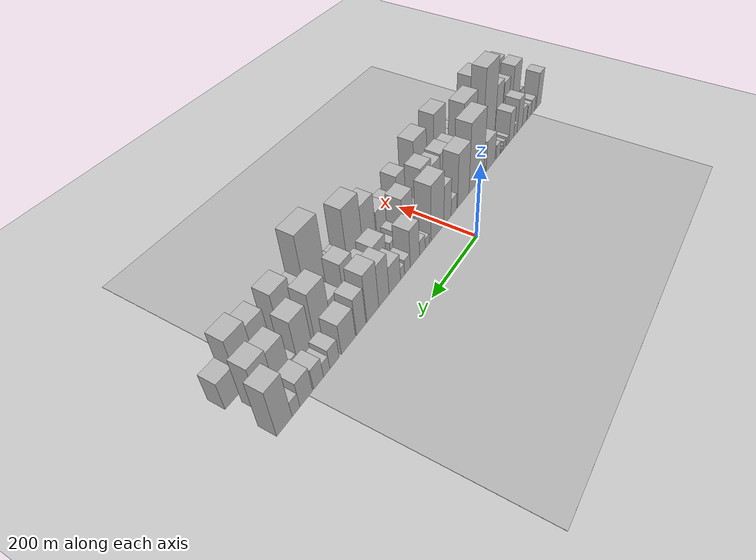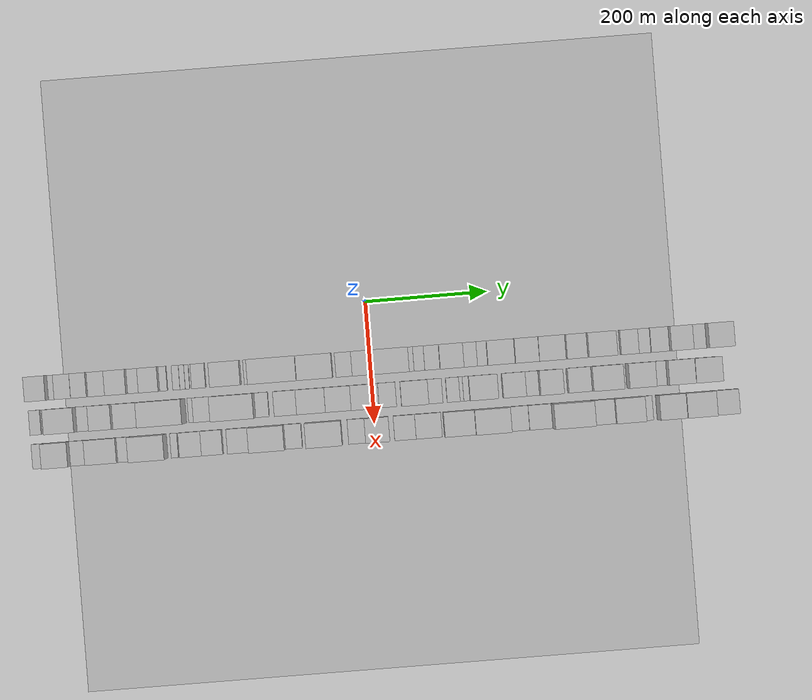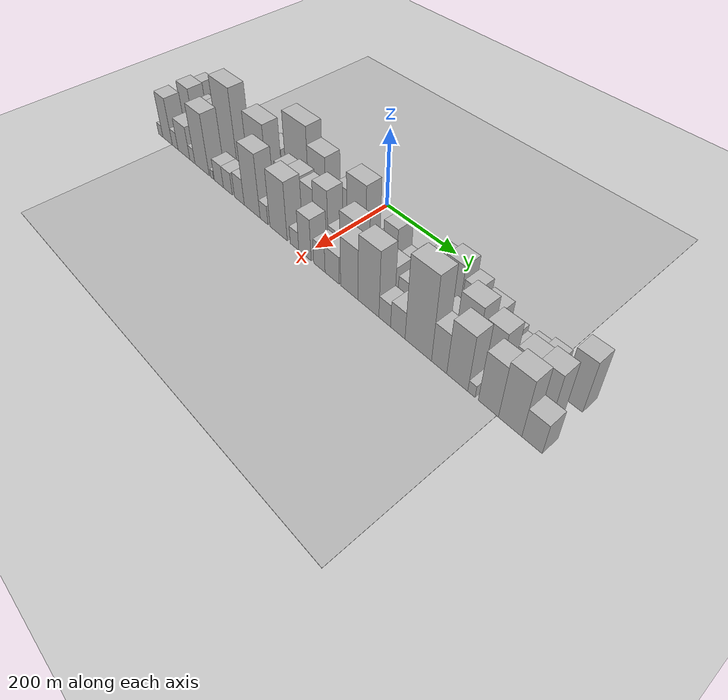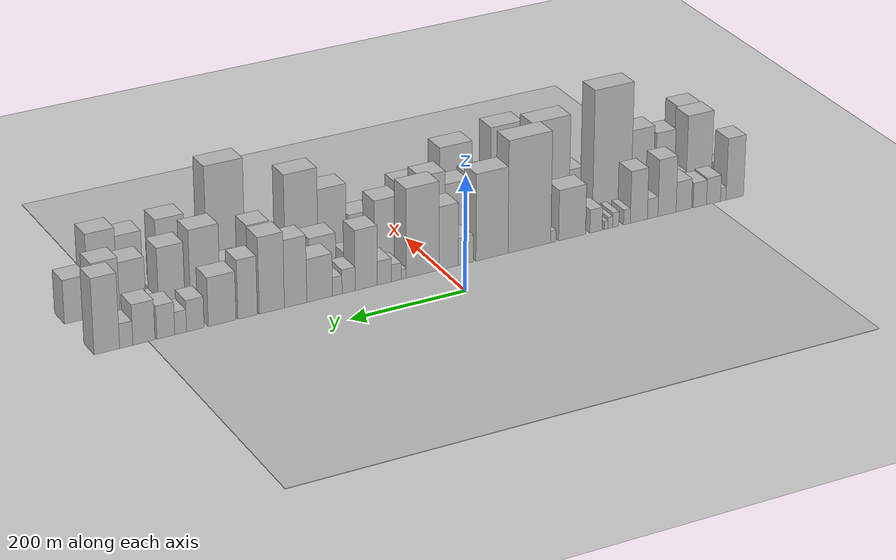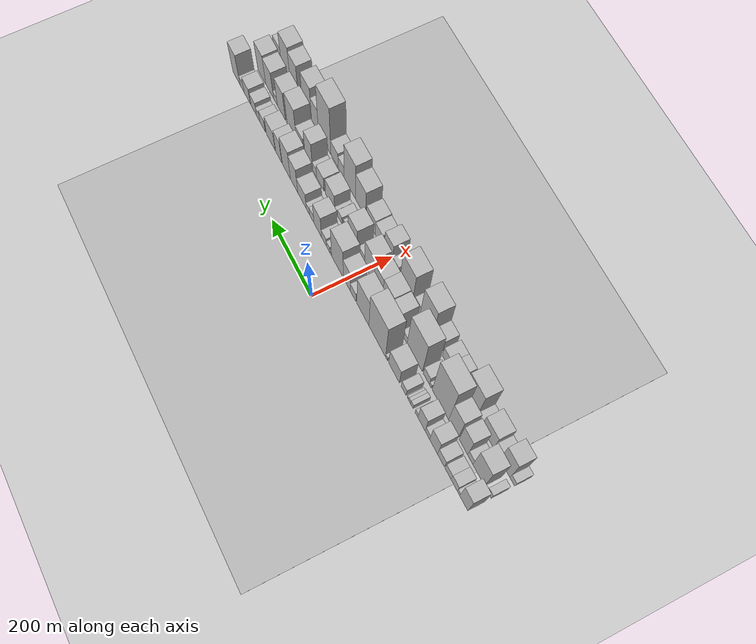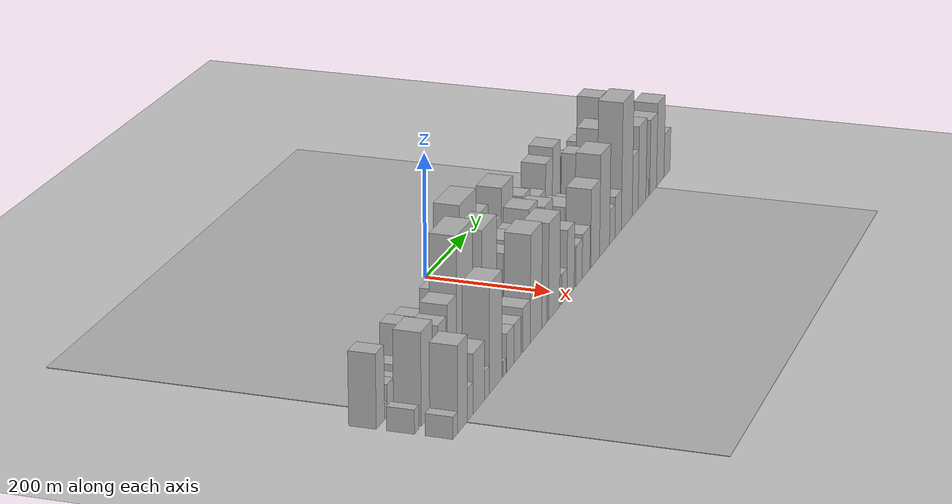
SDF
<?xml version="1.0" encoding="utf-8"?>

<sdf version="1.6">

   <world name="default">

      <gui fullscreen="0">

         <camera name="user_camera">

            <pose>-15 0 4.57585 0 0 0</pose>

            <view_controller>orbit</view_controller>

         </camera>

      </gui>

      <scene>

         <sky>

           <clouds>

             <speed>12</speed>

           </clouds>

         </sky>

         <ambient>0.4 0.4 0.4 1</ambient>

         <background>0.7 0.7 0.7 1</background>

         <shadows>1</shadows>

      </scene>

      <gravity>0 0 -9.8066</gravity>

      <magnetic_field>6e-06 2.3e-05 -4.2e-05</magnetic_field>

      <physics default="0" name="default_physics" type="ode">

         <ode>

            <solver>

               <type>quick</type>

               <iters>10</iters>

               <sor>1.0</sor>

               <use_dynamic_moi_rescaling>0</use_dynamic_moi_rescaling>

            </solver>

            <constraints>

               <cfm>0</cfm>

               <erp>0.2</erp>

               <contact_max_correcting_vel>100</contact_max_correcting_vel>

               <contact_surface_layer>0.001</contact_surface_layer>

            </constraints>

         </ode>

         <max_step_size>0.004</max_step_size>

         <real_time_factor>1</real_time_factor>

         <real_time_update_rate>250</real_time_update_rate>

      </physics>

      <light name="sun" type="directional">

         <cast_shadows>1</cast_shadows>

         <pose>0 0 10 0 0 0</pose>

         <diffuse>0.8 0.8 0.8 1</diffuse>

         <specular>0.2 0.2 0.2 1</specular>

         <attenuation>

            <range>1000</range>

            <constant>0.9</constant>

            <linear>0.01</linear>

            <quadratic>0.001</quadratic>

         </attenuation>

         <direction>-0.5 0.1 -0.9</direction>

      </light>

      <include>

         <name>ground_plane_1</name>

         <uri>model://HANNAS_ground_plane</uri>

         <pose>0 0 0  0 0 0</pose>

      </include>

      <include>

         <name>ground_plane_2</name>

         <uri>model://HANNAS_ground_plane</uri>

         <pose>100 0 0  0 0 0</pose>

      </include>

      <model name="building_1">

         <static>1</static>

         <pose frame="">100.0000 -543.0279 0 0.000000 0.000000 0.000000</pose>

         <link name="link">

            <pose frame="">0 0 55.50 0 0 0</pose>

            <collision name="collision">

               <geometry>

                  <box>

                     <size>40.0000 33.9441 111.0000</size>

                  </box>

               </geometry>

               <max_contacts>10</max_contacts>

               <surface>

                  <contact>

                     <ode/>

                  </contact>

                  <bounce/>

                  <friction>

                     <torsional>

                        <ode/>

                     </torsional>

                     <ode/>

                  </friction>

               </surface>

            </collision>

            <visual name="visual">

               <cast_shadows>0</cast_shadows>

               <geometry>

                  <box>

                     <size>40.0000 33.9441 111.0000</size>

                  </box>

               </geometry>

               <material>

                  <script>

                     <uri>model://HANNAS_wall/materials/scripts</uri>

                     <uri>model://HANNAS_wall/materials/textures</uri>

                     <name>vrc/HANNAS_wall</name>

                  </script>

               </material>

            </visual>

            <self_collide>0</self_collide>

            <enable_wind>0</enable_wind>

            <kinematic>0</kinematic>

         </link>

      </model>

      <model name="building_2">

         <static>1</static>

         <pose frame="">100.0000 -520.8618 0 0.000000 0.000000 0.000000</pose>

         <link name="link">

            <pose frame="">0 0 12.00 0 0 0</pose>

            <collision name="collision">

               <geometry>

                  <box>

                     <size>40.0000 10.3882 24.0000</size>

                  </box>

               </geometry>

               <max_contacts>10</max_contacts>

               <surface>

                  <contact>

                     <ode/>

                  </contact>

                  <bounce/>

                  <friction>

                     <torsional>

                        <ode/>

                     </torsional>

                     <ode/>

                  </friction>

               </surface>

            </collision>

            <visual name="visual">

               <cast_shadows>0</cast_shadows>

               <geometry>

                  <box>

                     <size>40.0000 10.3882 24.0000</size>

                  </box>

               </geometry>

               <material>

                  <script>

                     <uri>model://HANNAS_wall/materials/scripts</uri>

                     <uri>model://HANNAS_wall/materials/textures</uri>

                     <name>vrc/HANNAS_wall</name>

                  </script>

               </material>

            </visual>

            <self_collide>0</self_collide>

            <enable_wind>0</enable_wind>

            <kinematic>0</kinematic>

         </link>

      </model>

      <model name="building_3">

         <static>1</static>

         <pose frame="">100.0000 -502.2788 0 0.000000 0.000000 0.000000</pose>

         <link name="link">

            <pose frame="">0 0 24.00 0 0 0</pose>

            <collision name="collision">

               <geometry>

                  <box>

                     <size>40.0000 26.7778 48.0000</size>

                  </box>

               </geometry>

               <max_contacts>10</max_contacts>

               <surface>

                  <contact>

                     <ode/>

                  </contact>

                  <bounce/>

                  <friction>

                     <torsional>

                        <ode/>

                     </torsional>

                     <ode/>

                  </friction>

               </surface>

            </collision>

            <visual name="visual">

               <cast_shadows>0</cast_shadows>

               <geometry>

                  <box>

                     <size>40.0000 26.7778 48.0000</size>

                  </box>

               </geometry>

               <material>

                  <script>

                     <uri>model://HANNAS_wall/materials/scripts</uri>

                     <uri>model://HANNAS_wall/materials/textures</uri>

                     <name>vrc/HANNAS_wall</name>

                  </script>

               </material>

            </visual>

            <self_collide>0</self_collide>

            <enable_wind>0</enable_wind>

            <kinematic>0</kinematic>

         </link>

      </model>

      <model name="building_4">

         <static>1</static>

         <pose frame="">100.0000 -476.0945 0 0.000000 0.000000 0.000000</pose>

         <link name="link">

            <pose frame="">0 0 22.50 0 0 0</pose>

            <collision name="collision">

               <geometry>

                  <box>

                     <size>40.0000 25.5906 45.0000</size>

                  </box>

               </geometry>

               <max_contacts>10</max_contacts>

               <surface>

                  <contact>

                     <ode/>

                  </contact>

                  <bounce/>

                  <friction>

                     <torsional>

                        <ode/>

                     </torsional>

                     <ode/>

                  </friction>

               </surface>

            </collision>

            <visual name="visual">

               <cast_shadows>0</cast_shadows>

               <geometry>

                  <box>

                     <size>40.0000 25.5906 45.0000</size>

                  </box>

               </geometry>

               <material>

                  <script>

                     <uri>model://HANNAS_wall/materials/scripts</uri>

                     <uri>model://HANNAS_wall/materials/textures</uri>

                     <name>vrc/HANNAS_wall</name>

                  </script>

               </material>

            </visual>

            <self_collide>0</self_collide>

            <enable_wind>0</enable_wind>

            <kinematic>0</kinematic>

         </link>

      </model>

      <model name="building_5">

         <static>1</static>

         <pose frame="">100.0000 -445.5169 0 0.000000 0.000000 0.000000</pose>

         <link name="link">

            <pose frame="">0 0 27.00 0 0 0</pose>

            <collision name="collision">

               <geometry>

                  <box>

                     <size>40.0000 29.5647 54.0000</size>

                  </box>

               </geometry>

               <max_contacts>10</max_contacts>

               <surface>

                  <contact>

                     <ode/>

                  </contact>

                  <bounce/>

                  <friction>

                     <torsional>

                        <ode/>

                     </torsional>

                     <ode/>

                  </friction>

               </surface>

            </collision>

            <visual name="visual">

               <cast_shadows>0</cast_shadows>

               <geometry>

                  <box>

                     <size>40.0000 29.5647 54.0000</size>

                  </box>

               </geometry>

               <material>

                  <script>

                     <uri>model://HANNAS_wall/materials/scripts</uri>

                     <uri>model://HANNAS_wall/materials/textures</uri>

                     <name>vrc/HANNAS_wall</name>

                  </script>

               </material>

            </visual>

            <self_collide>0</self_collide>

            <enable_wind>0</enable_wind>

            <kinematic>0</kinematic>

         </link>

      </model>

      <model name="building_6">

         <static>1</static>

         <pose frame="">100.0000 -413.5826 0 0.000000 0.000000 0.000000</pose>

         <link name="link">

            <pose frame="">0 0 51.00 0 0 0</pose>

            <collision name="collision">

               <geometry>

                  <box>

                     <size>40.0000 34.3039 102.0000</size>

                  </box>

               </geometry>

               <max_contacts>10</max_contacts>

               <surface>

                  <contact>

                     <ode/>

                  </contact>

                  <bounce/>

                  <friction>

                     <torsional>

                        <ode/>

                     </torsional>

                     <ode/>

                  </friction>

               </surface>

            </collision>

            <visual name="visual">

               <cast_shadows>0</cast_shadows>

               <geometry>

                  <box>

                     <size>40.0000 34.3039 102.0000</size>

                  </box>

               </geometry>

               <material>

                  <script>

                     <uri>model://HANNAS_wall/materials/scripts</uri>

                     <uri>model://HANNAS_wall/materials/textures</uri>

                     <name>vrc/HANNAS_wall</name>

                  </script>

               </material>

            </visual>

            <self_collide>0</self_collide>

            <enable_wind>0</enable_wind>

            <kinematic>0</kinematic>

         </link>

      </model>

      <model name="building_7">

         <static>1</static>

         <pose frame="">100.0000 -386.4465 0 0.000000 0.000000 0.000000</pose>

         <link name="link">

            <pose frame="">0 0 18.00 0 0 0</pose>

            <collision name="collision">

               <geometry>

                  <box>

                     <size>40.0000 19.9681 36.0000</size>

                  </box>

               </geometry>

               <max_contacts>10</max_contacts>

               <surface>

                  <contact>

                     <ode/>

                  </contact>

                  <bounce/>

                  <friction>

                     <torsional>

                        <ode/>

                     </torsional>

                     <ode/>

                  </friction>

               </surface>

            </collision>

            <visual name="visual">

               <cast_shadows>0</cast_shadows>

               <geometry>

                  <box>

                     <size>40.0000 19.9681 36.0000</size>

                  </box>

               </geometry>

               <material>

                  <script>

                     <uri>model://HANNAS_wall/materials/scripts</uri>

                     <uri>model://HANNAS_wall/materials/textures</uri>

                     <name>vrc/HANNAS_wall</name>

                  </script>

               </material>

            </visual>

            <self_collide>0</self_collide>

            <enable_wind>0</enable_wind>

            <kinematic>0</kinematic>

         </link>

      </model>

      <model name="building_8">

         <static>1</static>

         <pose frame="">100.0000 -360.4686 0 0.000000 0.000000 0.000000</pose>

         <link name="link">

            <pose frame="">0 0 46.50 0 0 0</pose>

            <collision name="collision">

               <geometry>

                  <box>

                     <size>40.0000 31.9877 93.0000</size>

                  </box>

               </geometry>

               <max_contacts>10</max_contacts>

               <surface>

                  <contact>

                     <ode/>

                  </contact>

                  <bounce/>

                  <friction>

                     <torsional>

                        <ode/>

                     </torsional>

                     <ode/>

                  </friction>

               </surface>

            </collision>

            <visual name="visual">

               <cast_shadows>0</cast_shadows>

               <geometry>

                  <box>

                     <size>40.0000 31.9877 93.0000</size>

                  </box>

               </geometry>

               <material>

                  <script>

                     <uri>model://HANNAS_wall/materials/scripts</uri>

                     <uri>model://HANNAS_wall/materials/textures</uri>

                     <name>vrc/HANNAS_wall</name>

                  </script>

               </material>

            </visual>

            <self_collide>0</self_collide>

            <enable_wind>0</enable_wind>

            <kinematic>0</kinematic>

         </link>

      </model>

      <model name="building_9">

         <static>1</static>

         <pose frame="">100.0000 -338.2594 0 0.000000 0.000000 0.000000</pose>

         <link name="link">

            <pose frame="">0 0 13.50 0 0 0</pose>

            <collision name="collision">

               <geometry>

                  <box>

                     <size>40.0000 12.4307 27.0000</size>

                  </box>

               </geometry>

               <max_contacts>10</max_contacts>

               <surface>

                  <contact>

                     <ode/>

                  </contact>

                  <bounce/>

                  <friction>

                     <torsional>

                        <ode/>

                     </torsional>

                     <ode/>

                  </friction>

               </surface>

            </collision>

            <visual name="visual">

               <cast_shadows>0</cast_shadows>

               <geometry>

                  <box>

                     <size>40.0000 12.4307 27.0000</size>

                  </box>

               </geometry>

               <material>

                  <script>

                     <uri>model://HANNAS_wall/materials/scripts</uri>

                     <uri>model://HANNAS_wall/materials/textures</uri>

                     <name>vrc/HANNAS_wall</name>

                  </script>

               </material>

            </visual>

            <self_collide>0</self_collide>

            <enable_wind>0</enable_wind>

            <kinematic>0</kinematic>

         </link>

      </model>

      <model name="building_10">

         <static>1</static>

         <pose frame="">100.0000 -317.2501 0 0.000000 0.000000 0.000000</pose>

         <link name="link">

            <pose frame="">0 0 13.50 0 0 0</pose>

            <collision name="collision">

               <geometry>

                  <box>

                     <size>40.0000 11.5879 27.0000</size>

                  </box>

               </geometry>

               <max_contacts>10</max_contacts>

               <surface>

                  <contact>

                     <ode/>

                  </contact>

                  <bounce/>

                  <friction>

                     <torsional>

                        <ode/>

                     </torsional>

                     <ode/>

                  </friction>

               </surface>

            </collision>

            <visual name="visual">

               <cast_shadows>0</cast_shadows>

               <geometry>

                  <box>

                     <size>40.0000 11.5879 27.0000</size>

                  </box>

               </geometry>

               <material>

                  <script>

                     <uri>model://HANNAS_wall/materials/scripts</uri>

                     <uri>model://HANNAS_wall/materials/textures</uri>

                     <name>vrc/HANNAS_wall</name>

                  </script>

               </material>

            </visual>

            <self_collide>0</self_collide>

            <enable_wind>0</enable_wind>

            <kinematic>0</kinematic>

         </link>

      </model>

      <model name="building_11">

         <static>1</static>

         <pose frame="">100.0000 -307.1854 0 0.000000 0.000000 0.000000</pose>

         <link name="link">

            <pose frame="">0 0 10.50 0 0 0</pose>

            <collision name="collision">

               <geometry>

                  <box>

                     <size>40.0000 8.5415 21.0000</size>

                  </box>

               </geometry>

               <max_contacts>10</max_contacts>

               <surface>

                  <contact>

                     <ode/>

                  </contact>

                  <bounce/>

                  <friction>

                     <torsional>

                        <ode/>

                     </torsional>

                     <ode/>

                  </friction>

               </surface>

            </collision>

            <visual name="visual">

               <cast_shadows>0</cast_shadows>

               <geometry>

                  <box>

                     <size>40.0000 8.5415 21.0000</size>

                  </box>

               </geometry>

               <material>

                  <script>

                     <uri>model://HANNAS_wall/materials/scripts</uri>

                     <uri>model://HANNAS_wall/materials/textures</uri>

                     <name>vrc/HANNAS_wall</name>

                  </script>

               </material>

            </visual>

            <self_collide>0</self_collide>

            <enable_wind>0</enable_wind>

            <kinematic>0</kinematic>

         </link>

      </model>

      <model name="building_12">

         <static>1</static>

         <pose frame="">100.0000 -299.3905 0 0.000000 0.000000 0.000000</pose>

         <link name="link">

            <pose frame="">0 0 7.50 0 0 0</pose>

            <collision name="collision">

               <geometry>

                  <box>

                     <size>40.0000 7.0482 15.0000</size>

                  </box>

               </geometry>

               <max_contacts>10</max_contacts>

               <surface>

                  <contact>

                     <ode/>

                  </contact>

                  <bounce/>

                  <friction>

                     <torsional>

                        <ode/>

                     </torsional>

                     <ode/>

                  </friction>

               </surface>

            </collision>

            <visual name="visual">

               <cast_shadows>0</cast_shadows>

               <geometry>

                  <box>

                     <size>40.0000 7.0482 15.0000</size>

                  </box>

               </geometry>

               <material>

                  <script>

                     <uri>model://HANNAS_wall/materials/scripts</uri>

                     <uri>model://HANNAS_wall/materials/textures</uri>

                     <name>vrc/HANNAS_wall</name>

                  </script>

               </material>

            </visual>

            <self_collide>0</self_collide>

            <enable_wind>0</enable_wind>

            <kinematic>0</kinematic>

         </link>

      </model>

      <model name="building_13">

         <static>1</static>

         <pose frame="">100.0000 -280.5441 0 0.000000 0.000000 0.000000</pose>

         <link name="link">

            <pose frame="">0 0 21.00 0 0 0</pose>

            <collision name="collision">

               <geometry>

                  <box>

                     <size>40.0000 22.6448 42.0000</size>

                  </box>

               </geometry>

               <max_contacts>10</max_contacts>

               <surface>

                  <contact>

                     <ode/>

                  </contact>

                  <bounce/>

                  <friction>

                     <torsional>

                        <ode/>

                     </torsional>

                     <ode/>

                  </friction>

               </surface>

            </collision>

            <visual name="visual">

               <cast_shadows>0</cast_shadows>

               <geometry>

                  <box>

                     <size>40.0000 22.6448 42.0000</size>

                  </box>

               </geometry>

               <material>

                  <script>

                     <uri>model://HANNAS_wall/materials/scripts</uri>

                     <uri>model://HANNAS_wall/materials/textures</uri>

                     <name>vrc/HANNAS_wall</name>

                  </script>

               </material>

            </visual>

            <self_collide>0</self_collide>

            <enable_wind>0</enable_wind>

            <kinematic>0</kinematic>

         </link>

      </model>

      <model name="building_14">

         <static>1</static>

         <pose frame="">100.0000 -236.3965 0 0.000000 0.000000 0.000000</pose>

         <link name="link">

            <pose frame="">0 0 45.00 0 0 0</pose>

            <collision name="collision">

               <geometry>

                  <box>

                     <size>40.0000 49.6503 90.0000</size>

                  </box>

               </geometry>

               <max_contacts>10</max_contacts>

               <surface>

                  <contact>

                     <ode/>

                  </contact>

                  <bounce/>

                  <friction>

                     <torsional>

                        <ode/>

                     </torsional>

                     <ode/>

                  </friction>

               </surface>

            </collision>

            <visual name="visual">

               <cast_shadows>0</cast_shadows>

               <geometry>

                  <box>

                     <size>40.0000 49.6503 90.0000</size>

                  </box>

               </geometry>

               <material>

                  <script>

                     <uri>model://HANNAS_wall/materials/scripts</uri>

                     <uri>model://HANNAS_wall/materials/textures</uri>

                     <name>vrc/HANNAS_wall</name>

                  </script>

               </material>

            </visual>

            <self_collide>0</self_collide>

            <enable_wind>0</enable_wind>

            <kinematic>0</kinematic>

         </link>

      </model>

      <model name="building_15">

         <static>1</static>

         <pose frame="">100.0000 -201.8765 0 0.000000 0.000000 0.000000</pose>

         <link name="link">

            <pose frame="">0 0 10.50 0 0 0</pose>

            <collision name="collision">

               <geometry>

                  <box>

                     <size>40.0000 9.3897 21.0000</size>

                  </box>

               </geometry>

               <max_contacts>10</max_contacts>

               <surface>

                  <contact>

                     <ode/>

                  </contact>

                  <bounce/>

                  <friction>

                     <torsional>

                        <ode/>

                     </torsional>

                     <ode/>

                  </friction>

               </surface>

            </collision>

            <visual name="visual">

               <cast_shadows>0</cast_shadows>

               <geometry>

                  <box>

                     <size>40.0000 9.3897 21.0000</size>

                  </box>

               </geometry>

               <material>

                  <script>

                     <uri>model://HANNAS_wall/materials/scripts</uri>

                     <uri>model://HANNAS_wall/materials/textures</uri>

                     <name>vrc/HANNAS_wall</name>

                  </script>

               </material>

            </visual>

            <self_collide>0</self_collide>

            <enable_wind>0</enable_wind>

            <kinematic>0</kinematic>

         </link>

      </model>

      <model name="building_16">

         <static>1</static>

         <pose frame="">100.0000 -158.2002 0 0.000000 0.000000 0.000000</pose>

         <link name="link">

            <pose frame="">0 0 99.00 0 0 0</pose>

            <collision name="collision">

               <geometry>

                  <box>

                     <size>40.0000 77.9629 198.0000</size>

                  </box>

               </geometry>

               <max_contacts>10</max_contacts>

               <surface>

                  <contact>

                     <ode/>

                  </contact>

                  <bounce/>

                  <friction>

                     <torsional>

                        <ode/>

                     </torsional>

                     <ode/>

                  </friction>

               </surface>

            </collision>

            <visual name="visual">

               <cast_shadows>0</cast_shadows>

               <geometry>

                  <box>

                     <size>40.0000 77.9629 198.0000</size>

                  </box>

               </geometry>

               <material>

                  <script>

                     <uri>model://HANNAS_wall/materials/scripts</uri>

                     <uri>model://HANNAS_wall/materials/textures</uri>

                     <name>vrc/HANNAS_wall</name>

                  </script>

               </material>

            </visual>

            <self_collide>0</self_collide>

            <enable_wind>0</enable_wind>

            <kinematic>0</kinematic>

         </link>

      </model>

      <model name="building_17">

         <static>1</static>

         <pose frame="">100.0000 -90.4216 0 0.000000 0.000000 0.000000</pose>

         <link name="link">

            <pose frame="">0 0 76.50 0 0 0</pose>

            <collision name="collision">

               <geometry>

                  <box>

                     <size>40.0000 57.5943 153.0000</size>

                  </box>

               </geometry>

               <max_contacts>10</max_contacts>

               <surface>

                  <contact>

                     <ode/>

                  </contact>

                  <bounce/>

                  <friction>

                     <torsional>

                        <ode/>

                     </torsional>

                     <ode/>

                  </friction>

               </surface>

            </collision>

            <visual name="visual">

               <cast_shadows>0</cast_shadows>

               <geometry>

                  <box>

                     <size>40.0000 57.5943 153.0000</size>

                  </box>

               </geometry>

               <material>

                  <script>

                     <uri>model://HANNAS_wall/materials/scripts</uri>

                     <uri>model://HANNAS_wall/materials/textures</uri>

                     <name>vrc/HANNAS_wall</name>

                  </script>

               </material>

            </visual>

            <self_collide>0</self_collide>

            <enable_wind>0</enable_wind>

            <kinematic>0</kinematic>

         </link>

      </model>

      <model name="building_18">

         <static>1</static>

         <pose frame="">100.0000 -43.2304 0 0.000000 0.000000 0.000000</pose>

         <link name="link">

            <pose frame="">0 0 24.00 0 0 0</pose>

            <collision name="collision">

               <geometry>

                  <box>

                     <size>40.0000 26.7879 48.0000</size>

                  </box>

               </geometry>

               <max_contacts>10</max_contacts>

               <surface>

                  <contact>

                     <ode/>

                  </contact>

                  <bounce/>

                  <friction>

                     <torsional>

                        <ode/>

                     </torsional>

                     <ode/>

                  </friction>

               </surface>

            </collision>

            <visual name="visual">

               <cast_shadows>0</cast_shadows>

               <geometry>

                  <box>

                     <size>40.0000 26.7879 48.0000</size>

                  </box>

               </geometry>

               <material>

                  <script>

                     <uri>model://HANNAS_wall/materials/scripts</uri>

                     <uri>model://HANNAS_wall/materials/textures</uri>

                     <name>vrc/HANNAS_wall</name>

                  </script>

               </material>

            </visual>

            <self_collide>0</self_collide>

            <enable_wind>0</enable_wind>

            <kinematic>0</kinematic>

         </link>

      </model>

      <model name="building_19">

         <static>1</static>

         <pose frame="">100.0000 -12.8606 0 0.000000 0.000000 0.000000</pose>

         <link name="link">

            <pose frame="">0 0 55.50 0 0 0</pose>

            <collision name="collision">

               <geometry>

                  <box>

                     <size>40.0000 33.9517 111.0000</size>

                  </box>

               </geometry>

               <max_contacts>10</max_contacts>

               <surface>

                  <contact>

                     <ode/>

                  </contact>

                  <bounce/>

                  <friction>

                     <torsional>

                        <ode/>

                     </torsional>

                     <ode/>

                  </friction>

               </surface>

            </collision>

            <visual name="visual">

               <cast_shadows>0</cast_shadows>

               <geometry>

                  <box>

                     <size>40.0000 33.9517 111.0000</size>

                  </box>

               </geometry>

               <material>

                  <script>

                     <uri>model://HANNAS_wall/materials/scripts</uri>

                     <uri>model://HANNAS_wall/materials/textures</uri>

                     <name>vrc/HANNAS_wall</name>

                  </script>

               </material>

            </visual>

            <self_collide>0</self_collide>

            <enable_wind>0</enable_wind>

            <kinematic>0</kinematic>

         </link>

      </model>

      <model name="building_20">

         <static>1</static>

         <pose frame="">100.0000 33.2290 0 0.000000 0.000000 0.000000</pose>

         <link name="link">

            <pose frame="">0 0 78.00 0 0 0</pose>

            <collision name="collision">

               <geometry>

                  <box>

                     <size>40.0000 58.2275 156.0000</size>

                  </box>

               </geometry>

               <max_contacts>10</max_contacts>

               <surface>

                  <contact>

                     <ode/>

                  </contact>

                  <bounce/>

                  <friction>

                     <torsional>

                        <ode/>

                     </torsional>

                     <ode/>

                  </friction>

               </surface>

            </collision>

            <visual name="visual">

               <cast_shadows>0</cast_shadows>

               <geometry>

                  <box>

                     <size>40.0000 58.2275 156.0000</size>

                  </box>

               </geometry>

               <material>

                  <script>

                     <uri>model://HANNAS_wall/materials/scripts</uri>

                     <uri>model://HANNAS_wall/materials/textures</uri>

                     <name>vrc/HANNAS_wall</name>

                  </script>

               </material>

            </visual>

            <self_collide>0</self_collide>

            <enable_wind>0</enable_wind>

            <kinematic>0</kinematic>

         </link>

      </model>

      <model name="building_21">

         <static>1</static>

         <pose frame="">100.0000 66.6488 0 0.000000 0.000000 0.000000</pose>

         <link name="link">

            <pose frame="">0 0 9.00 0 0 0</pose>

            <collision name="collision">

               <geometry>

                  <box>

                     <size>40.0000 8.6122 18.0000</size>

                  </box>

               </geometry>

               <max_contacts>10</max_contacts>

               <surface>

                  <contact>

                     <ode/>

                  </contact>

                  <bounce/>

                  <friction>

                     <torsional>

                        <ode/>

                     </torsional>

                     <ode/>

                  </friction>

               </surface>

            </collision>

            <visual name="visual">

               <cast_shadows>0</cast_shadows>

               <geometry>

                  <box>

                     <size>40.0000 8.6122 18.0000</size>

                  </box>

               </geometry>

               <material>

                  <script>

                     <uri>model://HANNAS_wall/materials/scripts</uri>

                     <uri>model://HANNAS_wall/materials/textures</uri>

                     <name>vrc/HANNAS_wall</name>

                  </script>

               </material>

            </visual>

            <self_collide>0</self_collide>

            <enable_wind>0</enable_wind>

            <kinematic>0</kinematic>

         </link>

      </model>

      <model name="building_22">

         <static>1</static>

         <pose frame="">100.0000 79.5975 0 0.000000 0.000000 0.000000</pose>

         <link name="link">

            <pose frame="">0 0 15.00 0 0 0</pose>

            <collision name="collision">

               <geometry>

                  <box>

                     <size>40.0000 17.2851 30.0000</size>

                  </box>

               </geometry>

               <max_contacts>10</max_contacts>

               <surface>

                  <contact>

                     <ode/>

                  </contact>

                  <bounce/>

                  <friction>

                     <torsional>

                        <ode/>

                     </torsional>

                     <ode/>

                  </friction>

               </surface>

            </collision>

            <visual name="visual">

               <cast_shadows>0</cast_shadows>

               <geometry>

                  <box>

                     <size>40.0000 17.2851 30.0000</size>

                  </box>

               </geometry>

               <material>

                  <script>

                     <uri>model://HANNAS_wall/materials/scripts</uri>

                     <uri>model://HANNAS_wall/materials/textures</uri>

                     <name>vrc/HANNAS_wall</name>

                  </script>

               </material>

            </visual>

            <self_collide>0</self_collide>

            <enable_wind>0</enable_wind>

            <kinematic>0</kinematic>

         </link>

      </model>

      <model name="building_23">

         <static>1</static>

         <pose frame="">100.0000 100.5448 0 0.000000 0.000000 0.000000</pose>

         <link name="link">

            <pose frame="">0 0 21.00 0 0 0</pose>

            <collision name="collision">

               <geometry>

                  <box>

                     <size>40.0000 24.6096 42.0000</size>

                  </box>

               </geometry>

               <max_contacts>10</max_contacts>

               <surface>

                  <contact>

                     <ode/>

                  </contact>

                  <bounce/>

                  <friction>

                     <torsional>

                        <ode/>

                     </torsional>

                     <ode/>

                  </friction>

               </surface>

            </collision>

            <visual name="visual">

               <cast_shadows>0</cast_shadows>

               <geometry>

                  <box>

                     <size>40.0000 24.6096 42.0000</size>

                  </box>

               </geometry>

               <material>

                  <script>

                     <uri>model://HANNAS_wall/materials/scripts</uri>

                     <uri>model://HANNAS_wall/materials/textures</uri>

                     <name>vrc/HANNAS_wall</name>

                  </script>

               </material>

            </visual>

            <self_collide>0</self_collide>

            <enable_wind>0</enable_wind>

            <kinematic>0</kinematic>

         </link>

      </model>

      <model name="building_24">

         <static>1</static>

         <pose frame="">100.0000 132.1193 0 0.000000 0.000000 0.000000</pose>

         <link name="link">

            <pose frame="">0 0 52.50 0 0 0</pose>

            <collision name="collision">

               <geometry>

                  <box>

                     <size>40.0000 38.5394 105.0000</size>

                  </box>

               </geometry>

               <max_contacts>10</max_contacts>

               <surface>

                  <contact>

                     <ode/>

                  </contact>

                  <bounce/>

                  <friction>

                     <torsional>

                        <ode/>

                     </torsional>

                     <ode/>

                  </friction>

               </surface>

            </collision>

            <visual name="visual">

               <cast_shadows>0</cast_shadows>

               <geometry>

                  <box>

                     <size>40.0000 38.5394 105.0000</size>

                  </box>

               </geometry>

               <material>

                  <script>

                     <uri>model://HANNAS_wall/materials/scripts</uri>

                     <uri>model://HANNAS_wall/materials/textures</uri>

                     <name>vrc/HANNAS_wall</name>

                  </script>

               </material>

            </visual>

            <self_collide>0</self_collide>

            <enable_wind>0</enable_wind>

            <kinematic>0</kinematic>

         </link>

      </model>

      <model name="building_25">

         <static>1</static>

         <pose frame="">100.0000 162.7643 0 0.000000 0.000000 0.000000</pose>

         <link name="link">

            <pose frame="">0 0 21.00 0 0 0</pose>

            <collision name="collision">

               <geometry>

                  <box>

                     <size>40.0000 22.7505 42.0000</size>

                  </box>

               </geometry>

               <max_contacts>10</max_contacts>

               <surface>

                  <contact>

                     <ode/>

                  </contact>

                  <bounce/>

                  <friction>

                     <torsional>

                        <ode/>

                     </torsional>

                     <ode/>

                  </friction>

               </surface>

            </collision>

            <visual name="visual">

               <cast_shadows>0</cast_shadows>

               <geometry>

                  <box>

                     <size>40.0000 22.7505 42.0000</size>

                  </box>

               </geometry>

               <material>

                  <script>

                     <uri>model://HANNAS_wall/materials/scripts</uri>

                     <uri>model://HANNAS_wall/materials/textures</uri>

                     <name>vrc/HANNAS_wall</name>

                  </script>

               </material>

            </visual>

            <self_collide>0</self_collide>

            <enable_wind>0</enable_wind>

            <kinematic>0</kinematic>

         </link>

      </model>

      <model name="building_26">

         <static>1</static>

         <pose frame="">100.0000 182.4364 0 0.000000 0.000000 0.000000</pose>

         <link name="link">

            <pose frame="">0 0 16.50 0 0 0</pose>

            <collision name="collision">

               <geometry>

                  <box>

                     <size>40.0000 16.5937 33.0000</size>

                  </box>

               </geometry>

               <max_contacts>10</max_contacts>

               <surface>

                  <contact>

                     <ode/>

                  </contact>

                  <bounce/>

                  <friction>

                     <torsional>

                        <ode/>

                     </torsional>

                     <ode/>

                  </friction>

               </surface>

            </collision>

            <visual name="visual">

               <cast_shadows>0</cast_shadows>

               <geometry>

                  <box>

                     <size>40.0000 16.5937 33.0000</size>

                  </box>

               </geometry>

               <material>

                  <script>

                     <uri>model://HANNAS_wall/materials/scripts</uri>

                     <uri>model://HANNAS_wall/materials/textures</uri>

                     <name>vrc/HANNAS_wall</name>

                  </script>

               </material>

            </visual>

            <self_collide>0</self_collide>

            <enable_wind>0</enable_wind>

            <kinematic>0</kinematic>

         </link>

      </model>

      <model name="building_27">

         <static>1</static>

         <pose frame="">100.0000 212.7019 0 0.000000 0.000000 0.000000</pose>

         <link name="link">

            <pose frame="">0 0 37.50 0 0 0</pose>

            <collision name="collision">

               <geometry>

                  <box>

                     <size>40.0000 43.9373 75.0000</size>

                  </box>

               </geometry>

               <max_contacts>10</max_contacts>

               <surface>

                  <contact>

                     <ode/>

                  </contact>

                  <bounce/>

                  <friction>

                     <torsional>

                        <ode/>

                     </torsional>

                     <ode/>

                  </friction>

               </surface>

            </collision>

            <visual name="visual">

               <cast_shadows>0</cast_shadows>

               <geometry>

                  <box>

                     <size>40.0000 43.9373 75.0000</size>

                  </box>

               </geometry>

               <material>

                  <script>

                     <uri>model://HANNAS_wall/materials/scripts</uri>

                     <uri>model://HANNAS_wall/materials/textures</uri>

                     <name>vrc/HANNAS_wall</name>

                  </script>

               </material>

            </visual>

            <self_collide>0</self_collide>

            <enable_wind>0</enable_wind>

            <kinematic>0</kinematic>

         </link>

      </model>

      <model name="building_28">

         <static>1</static>

         <pose frame="">100.0000 253.8108 0 0.000000 0.000000 0.000000</pose>

         <link name="link">

            <pose frame="">0 0 58.50 0 0 0</pose>

            <collision name="collision">

               <geometry>

                  <box>

                     <size>40.0000 38.2804 117.0000</size>

                  </box>

               </geometry>

               <max_contacts>10</max_contacts>

               <surface>

                  <contact>

                     <ode/>

                  </contact>

                  <bounce/>

                  <friction>

                     <torsional>

                        <ode/>

                     </torsional>

                     <ode/>

                  </friction>

               </surface>

            </collision>

            <visual name="visual">

               <cast_shadows>0</cast_shadows>

               <geometry>

                  <box>

                     <size>40.0000 38.2804 117.0000</size>

                  </box>

               </geometry>

               <material>

                  <script>

                     <uri>model://HANNAS_wall/materials/scripts</uri>

                     <uri>model://HANNAS_wall/materials/textures</uri>

                     <name>vrc/HANNAS_wall</name>

                  </script>

               </material>

            </visual>

            <self_collide>0</self_collide>

            <enable_wind>0</enable_wind>

            <kinematic>0</kinematic>

         </link>

      </model>

      <model name="building_29">

         <static>1</static>

         <pose frame="">100.0000 294.3187 0 0.000000 0.000000 0.000000</pose>

         <link name="link">

            <pose frame="">0 0 66.00 0 0 0</pose>

            <collision name="collision">

               <geometry>

                  <box>

                     <size>40.0000 42.7354 132.0000</size>

                  </box>

               </geometry>

               <max_contacts>10</max_contacts>

               <surface>

                  <contact>

                     <ode/>

                  </contact>

                  <bounce/>

                  <friction>

                     <torsional>

                        <ode/>

                     </torsional>

                     <ode/>

                  </friction>

               </surface>

            </collision>

            <visual name="visual">

               <cast_shadows>0</cast_shadows>

               <geometry>

                  <box>

                     <size>40.0000 42.7354 132.0000</size>

                  </box>

               </geometry>

               <material>

                  <script>

                     <uri>model://HANNAS_wall/materials/scripts</uri>

                     <uri>model://HANNAS_wall/materials/textures</uri>

                     <name>vrc/HANNAS_wall</name>

                  </script>

               </material>

            </visual>

            <self_collide>0</self_collide>

            <enable_wind>0</enable_wind>

            <kinematic>0</kinematic>

         </link>

      </model>

      <model name="building_30">

         <static>1</static>

         <pose frame="">100.0000 335.1427 0 0.000000 0.000000 0.000000</pose>

         <link name="link">

            <pose frame="">0 0 51.00 0 0 0</pose>

            <collision name="collision">

               <geometry>

                  <box>

                     <size>40.0000 32.9125 102.0000</size>

                  </box>

               </geometry>

               <max_contacts>10</max_contacts>

               <surface>

                  <contact>

                     <ode/>

                  </contact>

                  <bounce/>

                  <friction>

                     <torsional>

                        <ode/>

                     </torsional>

                     <ode/>

                  </friction>

               </surface>

            </collision>

            <visual name="visual">

               <cast_shadows>0</cast_shadows>

               <geometry>

                  <box>

                     <size>40.0000 32.9125 102.0000</size>

                  </box>

               </geometry>

               <material>

                  <script>

                     <uri>model://HANNAS_wall/materials/scripts</uri>

                     <uri>model://HANNAS_wall/materials/textures</uri>

                     <name>vrc/HANNAS_wall</name>

                  </script>

               </material>

            </visual>

            <self_collide>0</self_collide>

            <enable_wind>0</enable_wind>

            <kinematic>0</kinematic>

         </link>

      </model>

      <model name="building_31">

         <static>1</static>

         <pose frame="">100.0000 377.8767 0 0.000000 0.000000 0.000000</pose>

         <link name="link">

            <pose frame="">0 0 42.00 0 0 0</pose>

            <collision name="collision">

               <geometry>

                  <box>

                     <size>40.0000 46.5556 84.0000</size>

                  </box>

               </geometry>

               <max_contacts>10</max_contacts>

               <surface>

                  <contact>

                     <ode/>

                  </contact>

                  <bounce/>

                  <friction>

                     <torsional>

                        <ode/>

                     </torsional>

                     <ode/>

                  </friction>

               </surface>

            </collision>

            <visual name="visual">

               <cast_shadows>0</cast_shadows>

               <geometry>

                  <box>

                     <size>40.0000 46.5556 84.0000</size>

                  </box>

               </geometry>

               <material>

                  <script>

                     <uri>model://HANNAS_wall/materials/scripts</uri>

                     <uri>model://HANNAS_wall/materials/textures</uri>

                     <name>vrc/HANNAS_wall</name>

                  </script>

               </material>

            </visual>

            <self_collide>0</self_collide>

            <enable_wind>0</enable_wind>

            <kinematic>0</kinematic>

         </link>

      </model>

      <model name="building_32">

         <static>1</static>

         <pose frame="">100.0000 422.6881 0 0.000000 0.000000 0.000000</pose>

         <link name="link">

            <pose frame="">0 0 27.00 0 0 0</pose>

            <collision name="collision">

               <geometry>

                  <box>

                     <size>40.0000 29.0671 54.0000</size>

                  </box>

               </geometry>

               <max_contacts>10</max_contacts>

               <surface>

                  <contact>

                     <ode/>

                  </contact>

                  <bounce/>

                  <friction>

                     <torsional>

                        <ode/>

                     </torsional>

                     <ode/>

                  </friction>

               </surface>

            </collision>

            <visual name="visual">

               <cast_shadows>0</cast_shadows>

               <geometry>

                  <box>

                     <size>40.0000 29.0671 54.0000</size>

                  </box>

               </geometry>

               <material>

                  <script>

                     <uri>model://HANNAS_wall/materials/scripts</uri>

                     <uri>model://HANNAS_wall/materials/textures</uri>

                     <name>vrc/HANNAS_wall</name>

                  </script>

               </material>

            </visual>

            <self_collide>0</self_collide>

            <enable_wind>0</enable_wind>

            <kinematic>0</kinematic>

         </link>

      </model>

      <model name="building_33">

         <static>1</static>

         <pose frame="">100.0000 447.0057 0 0.000000 0.000000 0.000000</pose>

         <link name="link">

            <pose frame="">0 0 19.50 0 0 0</pose>

            <collision name="collision">

               <geometry>

                  <box>

                     <size>40.0000 19.5682 39.0000</size>

                  </box>

               </geometry>

               <max_contacts>10</max_contacts>

               <surface>

                  <contact>

                     <ode/>

                  </contact>

                  <bounce/>

                  <friction>

                     <torsional>

                        <ode/>

                     </torsional>

                     <ode/>

                  </friction>

               </surface>

            </collision>

            <visual name="visual">

               <cast_shadows>0</cast_shadows>

               <geometry>

                  <box>

                     <size>40.0000 19.5682 39.0000</size>

                  </box>

               </geometry>

               <material>

                  <script>

                     <uri>model://HANNAS_wall/materials/scripts</uri>

                     <uri>model://HANNAS_wall/materials/textures</uri>

                     <name>vrc/HANNAS_wall</name>

                  </script>

               </material>

            </visual>

            <self_collide>0</self_collide>

            <enable_wind>0</enable_wind>

            <kinematic>0</kinematic>

         </link>

      </model>

      <model name="building_34">

         <static>1</static>

         <pose frame="">100.0000 471.5658 0 0.000000 0.000000 0.000000</pose>

         <link name="link">

            <pose frame="">0 0 28.50 0 0 0</pose>

            <collision name="collision">

               <geometry>

                  <box>

                     <size>40.0000 29.5520 57.0000</size>

                  </box>

               </geometry>

               <max_contacts>10</max_contacts>

               <surface>

                  <contact>

                     <ode/>

                  </contact>

                  <bounce/>

                  <friction>

                     <torsional>

                        <ode/>

                     </torsional>

                     <ode/>

                  </friction>

               </surface>

            </collision>

            <visual name="visual">

               <cast_shadows>0</cast_shadows>

               <geometry>

                  <box>

                     <size>40.0000 29.5520 57.0000</size>

                  </box>

               </geometry>

               <material>

                  <script>

                     <uri>model://HANNAS_wall/materials/scripts</uri>

                     <uri>model://HANNAS_wall/materials/textures</uri>

                     <name>vrc/HANNAS_wall</name>

                  </script>

               </material>

            </visual>

            <self_collide>0</self_collide>

            <enable_wind>0</enable_wind>

            <kinematic>0</kinematic>

         </link>

      </model>

      <model name="building_35">

         <static>1</static>

         <pose frame="">100.0000 507.5285 0 0.000000 0.000000 0.000000</pose>

         <link name="link">

            <pose frame="">0 0 34.50 0 0 0</pose>

            <collision name="collision">

               <geometry>

                  <box>

                     <size>40.0000 36.3733 69.0000</size>

                  </box>

               </geometry>

               <max_contacts>10</max_contacts>

               <surface>

                  <contact>

                     <ode/>

                  </contact>

                  <bounce/>

                  <friction>

                     <torsional>

                        <ode/>

                     </torsional>

                     <ode/>

                  </friction>

               </surface>

            </collision>

            <visual name="visual">

               <cast_shadows>0</cast_shadows>

               <geometry>

                  <box>

                     <size>40.0000 36.3733 69.0000</size>

                  </box>

               </geometry>

               <material>

                  <script>

                     <uri>model://HANNAS_wall/materials/scripts</uri>

                     <uri>model://HANNAS_wall/materials/textures</uri>

                     <name>vrc/HANNAS_wall</name>

                  </script>

               </material>

            </visual>

            <self_collide>0</self_collide>

            <enable_wind>0</enable_wind>

            <kinematic>0</kinematic>

         </link>

      </model>

      <model name="building_36">

         <static>1</static>

         <pose frame="">100.0000 536.4950 0 0.000000 0.000000 0.000000</pose>

         <link name="link">

            <pose frame="">0 0 21.00 0 0 0</pose>

            <collision name="collision">

               <geometry>

                  <box>

                     <size>40.0000 21.5597 42.0000</size>

                  </box>

               </geometry>

               <max_contacts>10</max_contacts>

               <surface>

                  <contact>

                     <ode/>

                  </contact>

                  <bounce/>

                  <friction>

                     <torsional>

                        <ode/>

                     </torsional>

                     <ode/>

                  </friction>

               </surface>

            </collision>

            <visual name="visual">

               <cast_shadows>0</cast_shadows>

               <geometry>

                  <box>

                     <size>40.0000 21.5597 42.0000</size>

                  </box>

               </geometry>

               <material>

                  <script>

                     <uri>model://HANNAS_wall/materials/scripts</uri>

                     <uri>model://HANNAS_wall/materials/textures</uri>

                     <name>vrc/HANNAS_wall</name>

                  </script>

               </material>

            </visual>

            <self_collide>0</self_collide>

            <enable_wind>0</enable_wind>

            <kinematic>0</kinematic>

         </link>

      </model>

      <model name="building_37">

         <static>1</static>

         <pose frame="">100.0000 568.0260 0 0.000000 0.000000 0.000000</pose>

         <link name="link">

            <pose frame="">0 0 64.50 0 0 0</pose>

            <collision name="collision">

               <geometry>

                  <box>

                     <size>40.0000 41.5023 129.0000</size>

                  </box>

               </geometry>

               <max_contacts>10</max_contacts>

               <surface>

                  <contact>

                     <ode/>

                  </contact>

                  <bounce/>

                  <friction>

                     <torsional>

                        <ode/>

                     </torsional>

                     <ode/>

                  </friction>

               </surface>

            </collision>

            <visual name="visual">

               <cast_shadows>0</cast_shadows>

               <geometry>

                  <box>

                     <size>40.0000 41.5023 129.0000</size>

                  </box>

               </geometry>

               <material>

                  <script>

                     <uri>model://HANNAS_wall/materials/scripts</uri>

                     <uri>model://HANNAS_wall/materials/textures</uri>

                     <name>vrc/HANNAS_wall</name>

                  </script>

               </material>

            </visual>

            <self_collide>0</self_collide>

            <enable_wind>0</enable_wind>

            <kinematic>0</kinematic>

         </link>

      </model>

      <model name="building_38">

         <static>1</static>

         <pose frame="">155.0000 -550.9318 0 0.000000 0.000000 0.000000</pose>

         <link name="link">

            <pose frame="">0 0 18.00 0 0 0</pose>

            <collision name="collision">

               <geometry>

                  <box>

                     <size>40.0000 18.1365 36.0000</size>

                  </box>

               </geometry>

               <max_contacts>10</max_contacts>

               <surface>

                  <contact>

                     <ode/>

                  </contact>

                  <bounce/>

                  <friction>

                     <torsional>

                        <ode/>

                     </torsional>

                     <ode/>

                  </friction>

               </surface>

            </collision>

            <visual name="visual">

               <cast_shadows>0</cast_shadows>

               <geometry>

                  <box>

                     <size>40.0000 18.1365 36.0000</size>

                  </box>

               </geometry>

               <material>

                  <script>

                     <uri>model://HANNAS_wall/materials/scripts</uri>

                     <uri>model://HANNAS_wall/materials/textures</uri>

                     <name>vrc/HANNAS_wall</name>

                  </script>

               </material>

            </visual>

            <self_collide>0</self_collide>

            <enable_wind>0</enable_wind>

            <kinematic>0</kinematic>

         </link>

      </model>

      <model name="building_39">

         <static>1</static>

         <pose frame="">155.0000 -507.3728 0 0.000000 0.000000 0.000000</pose>

         <link name="link">

            <pose frame="">0 0 69.00 0 0 0</pose>

            <collision name="collision">

               <geometry>

                  <box>

                     <size>40.0000 48.9813 138.0000</size>

                  </box>

               </geometry>

               <max_contacts>10</max_contacts>

               <surface>

                  <contact>

                     <ode/>

                  </contact>

                  <bounce/>

                  <friction>

                     <torsional>

                        <ode/>

                     </torsional>

                     <ode/>

                  </friction>

               </surface>

            </collision>

            <visual name="visual">

               <cast_shadows>0</cast_shadows>

               <geometry>

                  <box>

                     <size>40.0000 48.9813 138.0000</size>

                  </box>

               </geometry>

               <material>

                  <script>

                     <uri>model://HANNAS_wall/materials/scripts</uri>

                     <uri>model://HANNAS_wall/materials/textures</uri>

                     <name>vrc/HANNAS_wall</name>

                  </script>

               </material>

            </visual>

            <self_collide>0</self_collide>

            <enable_wind>0</enable_wind>

            <kinematic>0</kinematic>

         </link>

      </model>

      <model name="building_40">

         <static>1</static>

         <pose frame="">155.0000 -471.4999 0 0.000000 0.000000 0.000000</pose>

         <link name="link">

            <pose frame="">0 0 19.50 0 0 0</pose>

            <collision name="collision">

               <geometry>

                  <box>

                     <size>40.0000 22.7645 39.0000</size>

                  </box>

               </geometry>

               <max_contacts>10</max_contacts>

               <surface>

                  <contact>

                     <ode/>

                  </contact>

                  <bounce/>

                  <friction>

                     <torsional>

                        <ode/>

                     </torsional>

                     <ode/>

                  </friction>

               </surface>

            </collision>

            <visual name="visual">

               <cast_shadows>0</cast_shadows>

               <geometry>

                  <box>

                     <size>40.0000 22.7645 39.0000</size>

                  </box>

               </geometry>

               <material>

                  <script>

                     <uri>model://HANNAS_wall/materials/scripts</uri>

                     <uri>model://HANNAS_wall/materials/textures</uri>

                     <name>vrc/HANNAS_wall</name>

                  </script>

               </material>

            </visual>

            <self_collide>0</self_collide>

            <enable_wind>0</enable_wind>

            <kinematic>0</kinematic>

         </link>

      </model>

      <model name="building_41">

         <static>1</static>

         <pose frame="">155.0000 -441.9131 0 0.000000 0.000000 0.000000</pose>

         <link name="link">

            <pose frame="">0 0 60.00 0 0 0</pose>

            <collision name="collision">

               <geometry>

                  <box>

                     <size>40.0000 36.4091 120.0000</size>

                  </box>

               </geometry>

               <max_contacts>10</max_contacts>

               <surface>

                  <contact>

                     <ode/>

                  </contact>

                  <bounce/>

                  <friction>

                     <torsional>

                        <ode/>

                     </torsional>

                     <ode/>

                  </friction>

               </surface>

            </collision>

            <visual name="visual">

               <cast_shadows>0</cast_shadows>

               <geometry>

                  <box>

                     <size>40.0000 36.4091 120.0000</size>

                  </box>

               </geometry>

               <material>

                  <script>

                     <uri>model://HANNAS_wall/materials/scripts</uri>

                     <uri>model://HANNAS_wall/materials/textures</uri>

                     <name>vrc/HANNAS_wall</name>

                  </script>

               </material>

            </visual>

            <self_collide>0</self_collide>

            <enable_wind>0</enable_wind>

            <kinematic>0</kinematic>

         </link>

      </model>

      <model name="building_42">

         <static>1</static>

         <pose frame="">155.0000 -398.8538 0 0.000000 0.000000 0.000000</pose>

         <link name="link">

            <pose frame="">0 0 67.50 0 0 0</pose>

            <collision name="collision">

               <geometry>

                  <box>

                     <size>40.0000 41.7096 135.0000</size>

                  </box>

               </geometry>

               <max_contacts>10</max_contacts>

               <surface>

                  <contact>

                     <ode/>

                  </contact>

                  <bounce/>

                  <friction>

                     <torsional>

                        <ode/>

                     </torsional>

                     <ode/>

                  </friction>

               </surface>

            </collision>

            <visual name="visual">

               <cast_shadows>0</cast_shadows>

               <geometry>

                  <box>

                     <size>40.0000 41.7096 135.0000</size>

                  </box>

               </geometry>

               <material>

                  <script>

                     <uri>model://HANNAS_wall/materials/scripts</uri>

                     <uri>model://HANNAS_wall/materials/textures</uri>

                     <name>vrc/HANNAS_wall</name>

                  </script>

               </material>

            </visual>

            <self_collide>0</self_collide>

            <enable_wind>0</enable_wind>

            <kinematic>0</kinematic>

         </link>

      </model>

      <model name="building_43">

         <static>1</static>

         <pose frame="">155.0000 -341.8373 0 0.000000 0.000000 0.000000</pose>

         <link name="link">

            <pose frame="">0 0 111.00 0 0 0</pose>

            <collision name="collision">

               <geometry>

                  <box>

                     <size>40.0000 72.3234 222.0000</size>

                  </box>

               </geometry>

               <max_contacts>10</max_contacts>

               <surface>

                  <contact>

                     <ode/>

                  </contact>

                  <bounce/>

                  <friction>

                     <torsional>

                        <ode/>

                     </torsional>

                     <ode/>

                  </friction>

               </surface>

            </collision>

            <visual name="visual">

               <cast_shadows>0</cast_shadows>

               <geometry>

                  <box>

                     <size>40.0000 72.3234 222.0000</size>

                  </box>

               </geometry>

               <material>

                  <script>

                     <uri>model://HANNAS_wall/materials/scripts</uri>

                     <uri>model://HANNAS_wall/materials/textures</uri>

                     <name>vrc/HANNAS_wall</name>

                  </script>

               </material>

            </visual>

            <self_collide>0</self_collide>

            <enable_wind>0</enable_wind>

            <kinematic>0</kinematic>

         </link>

      </model>

      <model name="building_44">

         <static>1</static>

         <pose frame="">155.0000 -297.4022 0 0.000000 0.000000 0.000000</pose>

         <link name="link">

            <pose frame="">0 0 10.50 0 0 0</pose>

            <collision name="collision">

               <geometry>

                  <box>

                     <size>40.0000 8.5468 21.0000</size>

                  </box>

               </geometry>

               <max_contacts>10</max_contacts>

               <surface>

                  <contact>

                     <ode/>

                  </contact>

                  <bounce/>

                  <friction>

                     <torsional>

                        <ode/>

                     </torsional>

                     <ode/>

                  </friction>

               </surface>

            </collision>

            <visual name="visual">

               <cast_shadows>0</cast_shadows>

               <geometry>

                  <box>

                     <size>40.0000 8.5468 21.0000</size>

                  </box>

               </geometry>

               <material>

                  <script>

                     <uri>model://HANNAS_wall/materials/scripts</uri>

                     <uri>model://HANNAS_wall/materials/textures</uri>

                     <name>vrc/HANNAS_wall</name>

                  </script>

               </material>

            </visual>

            <self_collide>0</self_collide>

            <enable_wind>0</enable_wind>

            <kinematic>0</kinematic>

         </link>

      </model>

      <model name="building_45">

         <static>1</static>

         <pose frame="">155.0000 -279.4215 0 0.000000 0.000000 0.000000</pose>

         <link name="link">

            <pose frame="">0 0 24.00 0 0 0</pose>

            <collision name="collision">

               <geometry>

                  <box>

                     <size>40.0000 27.4146 48.0000</size>

                  </box>

               </geometry>

               <max_contacts>10</max_contacts>

               <surface>

                  <contact>

                     <ode/>

                  </contact>

                  <bounce/>

                  <friction>

                     <torsional>

                        <ode/>

                     </torsional>

                     <ode/>

                  </friction>

               </surface>

            </collision>

            <visual name="visual">

               <cast_shadows>0</cast_shadows>

               <geometry>

                  <box>

                     <size>40.0000 27.4146 48.0000</size>

                  </box>

               </geometry>

               <material>

                  <script>

                     <uri>model://HANNAS_wall/materials/scripts</uri>

                     <uri>model://HANNAS_wall/materials/textures</uri>

                     <name>vrc/HANNAS_wall</name>

                  </script>

               </material>

            </visual>

            <self_collide>0</self_collide>

            <enable_wind>0</enable_wind>

            <kinematic>0</kinematic>

         </link>

      </model>

      <model name="building_46">

         <static>1</static>

         <pose frame="">155.0000 -226.7624 0 0.000000 0.000000 0.000000</pose>

         <link name="link">

            <pose frame="">0 0 94.50 0 0 0</pose>

            <collision name="collision">

               <geometry>

                  <box>

                     <size>40.0000 69.9036 189.0000</size>

                  </box>

               </geometry>

               <max_contacts>10</max_contacts>

               <surface>

                  <contact>

                     <ode/>

                  </contact>

                  <bounce/>

                  <friction>

                     <torsional>

                        <ode/>

                     </torsional>

                     <ode/>

                  </friction>

               </surface>

            </collision>

            <visual name="visual">

               <cast_shadows>0</cast_shadows>

               <geometry>

                  <box>

                     <size>40.0000 69.9036 189.0000</size>

                  </box>

               </geometry>

               <material>

                  <script>

                     <uri>model://HANNAS_wall/materials/scripts</uri>

                     <uri>model://HANNAS_wall/materials/textures</uri>

                     <name>vrc/HANNAS_wall</name>

                  </script>

               </material>

            </visual>

            <self_collide>0</self_collide>

            <enable_wind>0</enable_wind>

            <kinematic>0</kinematic>

         </link>

      </model>

      <model name="building_47">

         <static>1</static>

         <pose frame="">155.0000 -180.9724 0 0.000000 0.000000 0.000000</pose>

         <link name="link">

            <pose frame="">0 0 19.50 0 0 0</pose>

            <collision name="collision">

               <geometry>

                  <box>

                     <size>40.0000 21.6764 39.0000</size>

                  </box>

               </geometry>

               <max_contacts>10</max_contacts>

               <surface>

                  <contact>

                     <ode/>

                  </contact>

                  <bounce/>

                  <friction>

                     <torsional>

                        <ode/>

                     </torsional>

                     <ode/>

                  </friction>

               </surface>

            </collision>

            <visual name="visual">

               <cast_shadows>0</cast_shadows>

               <geometry>

                  <box>

                     <size>40.0000 21.6764 39.0000</size>

                  </box>

               </geometry>

               <material>

                  <script>

                     <uri>model://HANNAS_wall/materials/scripts</uri>

                     <uri>model://HANNAS_wall/materials/textures</uri>

                     <name>vrc/HANNAS_wall</name>

                  </script>

               </material>

            </visual>

            <self_collide>0</self_collide>

            <enable_wind>0</enable_wind>

            <kinematic>0</kinematic>

         </link>

      </model>

      <model name="building_48">

         <static>1</static>

         <pose frame="">155.0000 -141.9574 0 0.000000 0.000000 0.000000</pose>

         <link name="link">

            <pose frame="">0 0 58.50 0 0 0</pose>

            <collision name="collision">

               <geometry>

                  <box>

                     <size>40.0000 36.3535 117.0000</size>

                  </box>

               </geometry>

               <max_contacts>10</max_contacts>

               <surface>

                  <contact>

                     <ode/>

                  </contact>

                  <bounce/>

                  <friction>

                     <torsional>

                        <ode/>

                     </torsional>

                     <ode/>

                  </friction>

               </surface>

            </collision>

            <visual name="visual">

               <cast_shadows>0</cast_shadows>

               <geometry>

                  <box>

                     <size>40.0000 36.3535 117.0000</size>

                  </box>

               </geometry>

               <material>

                  <script>

                     <uri>model://HANNAS_wall/materials/scripts</uri>

                     <uri>model://HANNAS_wall/materials/textures</uri>

                     <name>vrc/HANNAS_wall</name>

                  </script>

               </material>

            </visual>

            <self_collide>0</self_collide>

            <enable_wind>0</enable_wind>

            <kinematic>0</kinematic>

         </link>

      </model>

      <model name="building_49">

         <static>1</static>

         <pose frame="">155.0000 -100.5541 0 0.000000 0.000000 0.000000</pose>

         <link name="link">

            <pose frame="">0 0 61.50 0 0 0</pose>

            <collision name="collision">

               <geometry>

                  <box>

                     <size>40.0000 46.4531 123.0000</size>

                  </box>

               </geometry>

               <max_contacts>10</max_contacts>

               <surface>

                  <contact>

                     <ode/>

                  </contact>

                  <bounce/>

                  <friction>

                     <torsional>

                        <ode/>

                     </torsional>

                     <ode/>

                  </friction>

               </surface>

            </collision>

            <visual name="visual">

               <cast_shadows>0</cast_shadows>

               <geometry>

                  <box>

                     <size>40.0000 46.4531 123.0000</size>

                  </box>

               </geometry>

               <material>

                  <script>

                     <uri>model://HANNAS_wall/materials/scripts</uri>

                     <uri>model://HANNAS_wall/materials/textures</uri>

                     <name>vrc/HANNAS_wall</name>

                  </script>

               </material>

            </visual>

            <self_collide>0</self_collide>

            <enable_wind>0</enable_wind>

            <kinematic>0</kinematic>

         </link>

      </model>

      <model name="building_50">

         <static>1</static>

         <pose frame="">155.0000 -56.4309 0 0.000000 0.000000 0.000000</pose>

         <link name="link">

            <pose frame="">0 0 58.50 0 0 0</pose>

            <collision name="collision">

               <geometry>

                  <box>

                     <size>40.0000 41.7934 117.0000</size>

                  </box>

               </geometry>

               <max_contacts>10</max_contacts>

               <surface>

                  <contact>

                     <ode/>

                  </contact>

                  <bounce/>

                  <friction>

                     <torsional>

                        <ode/>

                     </torsional>

                     <ode/>

                  </friction>

               </surface>

            </collision>

            <visual name="visual">

               <cast_shadows>0</cast_shadows>

               <geometry>

                  <box>

                     <size>40.0000 41.7934 117.0000</size>

                  </box>

               </geometry>

               <material>

                  <script>

                     <uri>model://HANNAS_wall/materials/scripts</uri>

                     <uri>model://HANNAS_wall/materials/textures</uri>

                     <name>vrc/HANNAS_wall</name>

                  </script>

               </material>

            </visual>

            <self_collide>0</self_collide>

            <enable_wind>0</enable_wind>

            <kinematic>0</kinematic>

         </link>

      </model>

      <model name="building_51">

         <static>1</static>

         <pose frame="">155.0000 -12.9782 0 0.000000 0.000000 0.000000</pose>

         <link name="link">

            <pose frame="">0 0 70.50 0 0 0</pose>

            <collision name="collision">

               <geometry>

                  <box>

                     <size>40.0000 45.1121 141.0000</size>

                  </box>

               </geometry>

               <max_contacts>10</max_contacts>

               <surface>

                  <contact>

                     <ode/>

                  </contact>

                  <bounce/>

                  <friction>

                     <torsional>

                        <ode/>

                     </torsional>

                     <ode/>

                  </friction>

               </surface>

            </collision>

            <visual name="visual">

               <cast_shadows>0</cast_shadows>

               <geometry>

                  <box>

                     <size>40.0000 45.1121 141.0000</size>

                  </box>

               </geometry>

               <material>

                  <script>

                     <uri>model://HANNAS_wall/materials/scripts</uri>

                     <uri>model://HANNAS_wall/materials/textures</uri>

                     <name>vrc/HANNAS_wall</name>

                  </script>

               </material>

            </visual>

            <self_collide>0</self_collide>

            <enable_wind>0</enable_wind>

            <kinematic>0</kinematic>

         </link>

      </model>

      <model name="building_52">

         <static>1</static>

         <pose frame="">155.0000 23.7741 0 0.000000 0.000000 0.000000</pose>

         <link name="link">

            <pose frame="">0 0 27.00 0 0 0</pose>

            <collision name="collision">

               <geometry>

                  <box>

                     <size>40.0000 28.3925 54.0000</size>

                  </box>

               </geometry>

               <max_contacts>10</max_contacts>

               <surface>

                  <contact>

                     <ode/>

                  </contact>

                  <bounce/>

                  <friction>

                     <torsional>

                        <ode/>

                     </torsional>

                     <ode/>

                  </friction>

               </surface>

            </collision>

            <visual name="visual">

               <cast_shadows>0</cast_shadows>

               <geometry>

                  <box>

                     <size>40.0000 28.3925 54.0000</size>

                  </box>

               </geometry>

               <material>

                  <script>

                     <uri>model://HANNAS_wall/materials/scripts</uri>

                     <uri>model://HANNAS_wall/materials/textures</uri>

                     <name>vrc/HANNAS_wall</name>

                  </script>

               </material>

            </visual>

            <self_collide>0</self_collide>

            <enable_wind>0</enable_wind>

            <kinematic>0</kinematic>

         </link>

      </model>

      <model name="building_53">

         <static>1</static>

         <pose frame="">155.0000 67.9589 0 0.000000 0.000000 0.000000</pose>

         <link name="link">

            <pose frame="">0 0 58.50 0 0 0</pose>

            <collision name="collision">

               <geometry>

                  <box>

                     <size>40.0000 43.9771 117.0000</size>

                  </box>

               </geometry>

               <max_contacts>10</max_contacts>

               <surface>

                  <contact>

                     <ode/>

                  </contact>

                  <bounce/>

                  <friction>

                     <torsional>

                        <ode/>

                     </torsional>

                     <ode/>

                  </friction>

               </surface>

            </collision>

            <visual name="visual">

               <cast_shadows>0</cast_shadows>

               <geometry>

                  <box>

                     <size>40.0000 43.9771 117.0000</size>

                  </box>

               </geometry>

               <material>

                  <script>

                     <uri>model://HANNAS_wall/materials/scripts</uri>

                     <uri>model://HANNAS_wall/materials/textures</uri>

                     <name>vrc/HANNAS_wall</name>

                  </script>

               </material>

            </visual>

            <self_collide>0</self_collide>

            <enable_wind>0</enable_wind>

            <kinematic>0</kinematic>

         </link>

      </model>

      <model name="building_54">

         <static>1</static>

         <pose frame="">155.0000 101.7364 0 0.000000 0.000000 0.000000</pose>

         <link name="link">

            <pose frame="">0 0 21.00 0 0 0</pose>

            <collision name="collision">

               <geometry>

                  <box>

                     <size>40.0000 23.5777 42.0000</size>

                  </box>

               </geometry>

               <max_contacts>10</max_contacts>

               <surface>

                  <contact>

                     <ode/>

                  </contact>

                  <bounce/>

                  <friction>

                     <torsional>

                        <ode/>

                     </torsional>

                     <ode/>

                  </friction>

               </surface>

            </collision>

            <visual name="visual">

               <cast_shadows>0</cast_shadows>

               <geometry>

                  <box>

                     <size>40.0000 23.5777 42.0000</size>

                  </box>

               </geometry>

               <material>

                  <script>

                     <uri>model://HANNAS_wall/materials/scripts</uri>

                     <uri>model://HANNAS_wall/materials/textures</uri>

                     <name>vrc/HANNAS_wall</name>

                  </script>

               </material>

            </visual>

            <self_collide>0</self_collide>

            <enable_wind>0</enable_wind>

            <kinematic>0</kinematic>

         </link>

      </model>

      <model name="building_55">

         <static>1</static>

         <pose frame="">155.0000 131.0932 0 0.000000 0.000000 0.000000</pose>

         <link name="link">

            <pose frame="">0 0 18.00 0 0 0</pose>

            <collision name="collision">

               <geometry>

                  <box>

                     <size>40.0000 21.1361 36.0000</size>

                  </box>

               </geometry>

               <max_contacts>10</max_contacts>

               <surface>

                  <contact>

                     <ode/>

                  </contact>

                  <bounce/>

                  <friction>

                     <torsional>

                        <ode/>

                     </torsional>

                     <ode/>

                  </friction>

               </surface>

            </collision>

            <visual name="visual">

               <cast_shadows>0</cast_shadows>

               <geometry>

                  <box>

                     <size>40.0000 21.1361 36.0000</size>

                  </box>

               </geometry>

               <material>

                  <script>

                     <uri>model://HANNAS_wall/materials/scripts</uri>

                     <uri>model://HANNAS_wall/materials/textures</uri>

                     <name>vrc/HANNAS_wall</name>

                  </script>

               </material>

            </visual>

            <self_collide>0</self_collide>

            <enable_wind>0</enable_wind>

            <kinematic>0</kinematic>

         </link>

      </model>

      <model name="building_56">

         <static>1</static>

         <pose frame="">155.0000 144.7560 0 0.000000 0.000000 0.000000</pose>

         <link name="link">

            <pose frame="">0 0 7.50 0 0 0</pose>

            <collision name="collision">

               <geometry>

                  <box>

                     <size>40.0000 6.1895 15.0000</size>

                  </box>

               </geometry>

               <max_contacts>10</max_contacts>

               <surface>

                  <contact>

                     <ode/>

                  </contact>

                  <bounce/>

                  <friction>

                     <torsional>

                        <ode/>

                     </torsional>

                     <ode/>

                  </friction>

               </surface>

            </collision>

            <visual name="visual">

               <cast_shadows>0</cast_shadows>

               <geometry>

                  <box>

                     <size>40.0000 6.1895 15.0000</size>

                  </box>

               </geometry>

               <material>

                  <script>

                     <uri>model://HANNAS_wall/materials/scripts</uri>

                     <uri>model://HANNAS_wall/materials/textures</uri>

                     <name>vrc/HANNAS_wall</name>

                  </script>

               </material>

            </visual>

            <self_collide>0</self_collide>

            <enable_wind>0</enable_wind>

            <kinematic>0</kinematic>

         </link>

      </model>

      <model name="building_57">

         <static>1</static>

         <pose frame="">155.0000 152.7059 0 0.000000 0.000000 0.000000</pose>

         <link name="link">

            <pose frame="">0 0 10.50 0 0 0</pose>

            <collision name="collision">

               <geometry>

                  <box>

                     <size>40.0000 9.7101 21.0000</size>

                  </box>

               </geometry>

               <max_contacts>10</max_contacts>

               <surface>

                  <contact>

                     <ode/>

                  </contact>

                  <bounce/>

                  <friction>

                     <torsional>

                        <ode/>

                     </torsional>

                     <ode/>

                  </friction>

               </surface>

            </collision>

            <visual name="visual">

               <cast_shadows>0</cast_shadows>

               <geometry>

                  <box>

                     <size>40.0000 9.7101 21.0000</size>

                  </box>

               </geometry>

               <material>

                  <script>

                     <uri>model://HANNAS_wall/materials/scripts</uri>

                     <uri>model://HANNAS_wall/materials/textures</uri>

                     <name>vrc/HANNAS_wall</name>

                  </script>

               </material>

            </visual>

            <self_collide>0</self_collide>

            <enable_wind>0</enable_wind>

            <kinematic>0</kinematic>

         </link>

      </model>

      <model name="building_58">

         <static>1</static>

         <pose frame="">155.0000 180.6804 0 0.000000 0.000000 0.000000</pose>

         <link name="link">

            <pose frame="">0 0 39.00 0 0 0</pose>

            <collision name="collision">

               <geometry>

                  <box>

                     <size>40.0000 46.2390 78.0000</size>

                  </box>

               </geometry>

               <max_contacts>10</max_contacts>

               <surface>

                  <contact>

                     <ode/>

                  </contact>

                  <bounce/>

                  <friction>

                     <torsional>

                        <ode/>

                     </torsional>

                     <ode/>

                  </friction>

               </surface>

            </collision>

            <visual name="visual">

               <cast_shadows>0</cast_shadows>

               <geometry>

                  <box>

                     <size>40.0000 46.2390 78.0000</size>

                  </box>

               </geometry>

               <material>

                  <script>

                     <uri>model://HANNAS_wall/materials/scripts</uri>

                     <uri>model://HANNAS_wall/materials/textures</uri>

                     <name>vrc/HANNAS_wall</name>

                  </script>

               </material>

            </visual>

            <self_collide>0</self_collide>

            <enable_wind>0</enable_wind>

            <kinematic>0</kinematic>

         </link>

      </model>

      <model name="building_59">

         <static>1</static>

         <pose frame="">155.0000 230.5927 0 0.000000 0.000000 0.000000</pose>

         <link name="link">

            <pose frame="">0 0 33.00 0 0 0</pose>

            <collision name="collision">

               <geometry>

                  <box>

                     <size>40.0000 37.5855 66.0000</size>

                  </box>

               </geometry>

               <max_contacts>10</max_contacts>

               <surface>

                  <contact>

                     <ode/>

                  </contact>

                  <bounce/>

                  <friction>

                     <torsional>

                        <ode/>

                     </torsional>

                     <ode/>

                  </friction>

               </surface>

            </collision>

            <visual name="visual">

               <cast_shadows>0</cast_shadows>

               <geometry>

                  <box>

                     <size>40.0000 37.5855 66.0000</size>

                  </box>

               </geometry>

               <material>

                  <script>

                     <uri>model://HANNAS_wall/materials/scripts</uri>

                     <uri>model://HANNAS_wall/materials/textures</uri>

                     <name>vrc/HANNAS_wall</name>

                  </script>

               </material>

            </visual>

            <self_collide>0</self_collide>

            <enable_wind>0</enable_wind>

            <kinematic>0</kinematic>

         </link>

      </model>

      <model name="building_60">

         <static>1</static>

         <pose frame="">155.0000 260.0713 0 0.000000 0.000000 0.000000</pose>

         <link name="link">

            <pose frame="">0 0 21.00 0 0 0</pose>

            <collision name="collision">

               <geometry>

                  <box>

                     <size>40.0000 21.3718 42.0000</size>

                  </box>

               </geometry>

               <max_contacts>10</max_contacts>

               <surface>

                  <contact>

                     <ode/>

                  </contact>

                  <bounce/>

                  <friction>

                     <torsional>

                        <ode/>

                     </torsional>

                     <ode/>

                  </friction>

               </surface>

            </collision>

            <visual name="visual">

               <cast_shadows>0</cast_shadows>

               <geometry>

                  <box>

                     <size>40.0000 21.3718 42.0000</size>

                  </box>

               </geometry>

               <material>

                  <script>

                     <uri>model://HANNAS_wall/materials/scripts</uri>

                     <uri>model://HANNAS_wall/materials/textures</uri>

                     <name>vrc/HANNAS_wall</name>

                  </script>

               </material>

            </visual>

            <self_collide>0</self_collide>

            <enable_wind>0</enable_wind>

            <kinematic>0</kinematic>

         </link>

      </model>

      <model name="building_61">

         <static>1</static>

         <pose frame="">155.0000 289.8224 0 0.000000 0.000000 0.000000</pose>

         <link name="link">

            <pose frame="">0 0 63.00 0 0 0</pose>

            <collision name="collision">

               <geometry>

                  <box>

                     <size>40.0000 38.1304 126.0000</size>

                  </box>

               </geometry>

               <max_contacts>10</max_contacts>

               <surface>

                  <contact>

                     <ode/>

                  </contact>

                  <bounce/>

                  <friction>

                     <torsional>

                        <ode/>

                     </torsional>

                     <ode/>

                  </friction>

               </surface>

            </collision>

            <visual name="visual">

               <cast_shadows>0</cast_shadows>

               <geometry>

                  <box>

                     <size>40.0000 38.1304 126.0000</size>

                  </box>

               </geometry>

               <material>

                  <script>

                     <uri>model://HANNAS_wall/materials/scripts</uri>

                     <uri>model://HANNAS_wall/materials/textures</uri>

                     <name>vrc/HANNAS_wall</name>

                  </script>

               </material>

            </visual>

            <self_collide>0</self_collide>

            <enable_wind>0</enable_wind>

            <kinematic>0</kinematic>

         </link>

      </model>

      <model name="building_62">

         <static>1</static>

         <pose frame="">155.0000 336.8014 0 0.000000 0.000000 0.000000</pose>

         <link name="link">

            <pose frame="">0 0 36.00 0 0 0</pose>

            <collision name="collision">

               <geometry>

                  <box>

                     <size>40.0000 37.8276 72.0000</size>

                  </box>

               </geometry>

               <max_contacts>10</max_contacts>

               <surface>

                  <contact>

                     <ode/>

                  </contact>

                  <bounce/>

                  <friction>

                     <torsional>

                        <ode/>

                     </torsional>

                     <ode/>

                  </friction>

               </surface>

            </collision>

            <visual name="visual">

               <cast_shadows>0</cast_shadows>

               <geometry>

                  <box>

                     <size>40.0000 37.8276 72.0000</size>

                  </box>

               </geometry>

               <material>

                  <script>

                     <uri>model://HANNAS_wall/materials/scripts</uri>

                     <uri>model://HANNAS_wall/materials/textures</uri>

                     <name>vrc/HANNAS_wall</name>

                  </script>

               </material>

            </visual>

            <self_collide>0</self_collide>

            <enable_wind>0</enable_wind>

            <kinematic>0</kinematic>

         </link>

      </model>

      <model name="building_63">

         <static>1</static>

         <pose frame="">155.0000 380.7532 0 0.000000 0.000000 0.000000</pose>

         <link name="link">

            <pose frame="">0 0 70.50 0 0 0</pose>

            <collision name="collision">

               <geometry>

                  <box>

                     <size>40.0000 50.0759 141.0000</size>

                  </box>

               </geometry>

               <max_contacts>10</max_contacts>

               <surface>

                  <contact>

                     <ode/>

                  </contact>

                  <bounce/>

                  <friction>

                     <torsional>

                        <ode/>

                     </torsional>

                     <ode/>

                  </friction>

               </surface>

            </collision>

            <visual name="visual">

               <cast_shadows>0</cast_shadows>

               <geometry>

                  <box>

                     <size>40.0000 50.0759 141.0000</size>

                  </box>

               </geometry>

               <material>

                  <script>

                     <uri>model://HANNAS_wall/materials/scripts</uri>

                     <uri>model://HANNAS_wall/materials/textures</uri>

                     <name>vrc/HANNAS_wall</name>

                  </script>

               </material>

            </visual>

            <self_collide>0</self_collide>

            <enable_wind>0</enable_wind>

            <kinematic>0</kinematic>

         </link>

      </model>

      <model name="building_64">

         <static>1</static>

         <pose frame="">155.0000 436.6621 0 0.000000 0.000000 0.000000</pose>

         <link name="link">

            <pose frame="">0 0 61.50 0 0 0</pose>

            <collision name="collision">

               <geometry>

                  <box>

                     <size>40.0000 43.7420 123.0000</size>

                  </box>

               </geometry>

               <max_contacts>10</max_contacts>

               <surface>

                  <contact>

                     <ode/>

                  </contact>

                  <bounce/>

                  <friction>

                     <torsional>

                        <ode/>

                     </torsional>

                     <ode/>

                  </friction>

               </surface>

            </collision>

            <visual name="visual">

               <cast_shadows>0</cast_shadows>

               <geometry>

                  <box>

                     <size>40.0000 43.7420 123.0000</size>

                  </box>

               </geometry>

               <material>

                  <script>

                     <uri>model://HANNAS_wall/materials/scripts</uri>

                     <uri>model://HANNAS_wall/materials/textures</uri>

                     <name>vrc/HANNAS_wall</name>

                  </script>

               </material>

            </visual>

            <self_collide>0</self_collide>

            <enable_wind>0</enable_wind>

            <kinematic>0</kinematic>

         </link>

      </model>

      <model name="building_65">

         <static>1</static>

         <pose frame="">155.0000 468.9399 0 0.000000 0.000000 0.000000</pose>

         <link name="link">

            <pose frame="">0 0 18.00 0 0 0</pose>

            <collision name="collision">

               <geometry>

                  <box>

                     <size>40.0000 20.8135 36.0000</size>

                  </box>

               </geometry>

               <max_contacts>10</max_contacts>

               <surface>

                  <contact>

                     <ode/>

                  </contact>

                  <bounce/>

                  <friction>

                     <torsional>

                        <ode/>

                     </torsional>

                     <ode/>

                  </friction>

               </surface>

            </collision>

            <visual name="visual">

               <cast_shadows>0</cast_shadows>

               <geometry>

                  <box>

                     <size>40.0000 20.8135 36.0000</size>

                  </box>

               </geometry>

               <material>

                  <script>

                     <uri>model://HANNAS_wall/materials/scripts</uri>

                     <uri>model://HANNAS_wall/materials/textures</uri>

                     <name>vrc/HANNAS_wall</name>

                  </script>

               </material>

            </visual>

            <self_collide>0</self_collide>

            <enable_wind>0</enable_wind>

            <kinematic>0</kinematic>

         </link>

      </model>

      <model name="building_66">

         <static>1</static>

         <pose frame="">155.0000 500.9009 0 0.000000 0.000000 0.000000</pose>

         <link name="link">

            <pose frame="">0 0 57.00 0 0 0</pose>

            <collision name="collision">

               <geometry>

                  <box>

                     <size>40.0000 43.1086 114.0000</size>

                  </box>

               </geometry>

               <max_contacts>10</max_contacts>

               <surface>

                  <contact>

                     <ode/>

                  </contact>

                  <bounce/>

                  <friction>

                     <torsional>

                        <ode/>

                     </torsional>

                     <ode/>

                  </friction>

               </surface>

            </collision>

            <visual name="visual">

               <cast_shadows>0</cast_shadows>

               <geometry>

                  <box>

                     <size>40.0000 43.1086 114.0000</size>

                  </box>

               </geometry>

               <material>

                  <script>

                     <uri>model://HANNAS_wall/materials/scripts</uri>

                     <uri>model://HANNAS_wall/materials/textures</uri>

                     <name>vrc/HANNAS_wall</name>

                  </script>

               </material>

            </visual>

            <self_collide>0</self_collide>

            <enable_wind>0</enable_wind>

            <kinematic>0</kinematic>

         </link>

      </model>

      <model name="building_67">

         <static>1</static>

         <pose frame="">155.0000 544.3453 0 0.000000 0.000000 0.000000</pose>

         <link name="link">

            <pose frame="">0 0 61.50 0 0 0</pose>

            <collision name="collision">

               <geometry>

                  <box>

                     <size>40.0000 43.7800 123.0000</size>

                  </box>

               </geometry>

               <max_contacts>10</max_contacts>

               <surface>

                  <contact>

                     <ode/>

                  </contact>

                  <bounce/>

                  <friction>

                     <torsional>

                        <ode/>

                     </torsional>

                     <ode/>

                  </friction>

               </surface>

            </collision>

            <visual name="visual">

               <cast_shadows>0</cast_shadows>

               <geometry>

                  <box>

                     <size>40.0000 43.7800 123.0000</size>

                  </box>

               </geometry>

               <material>

                  <script>

                     <uri>model://HANNAS_wall/materials/scripts</uri>

                     <uri>model://HANNAS_wall/materials/textures</uri>

                     <name>vrc/HANNAS_wall</name>

                  </script>

               </material>

            </visual>

            <self_collide>0</self_collide>

            <enable_wind>0</enable_wind>

            <kinematic>0</kinematic>

         </link>

      </model>

      <model name="building_68">

         <static>1</static>

         <pose frame="">210.0000 -550.1332 0 0.000000 0.000000 0.000000</pose>

         <link name="link">

            <pose frame="">0 0 16.50 0 0 0</pose>

            <collision name="collision">

               <geometry>

                  <box>

                     <size>40.0000 19.7337 33.0000</size>

                  </box>

               </geometry>

               <max_contacts>10</max_contacts>

               <surface>

                  <contact>

                     <ode/>

                  </contact>

                  <bounce/>

                  <friction>

                     <torsional>

                        <ode/>

                     </torsional>

                     <ode/>

                  </friction>

               </surface>

            </collision>

            <visual name="visual">

               <cast_shadows>0</cast_shadows>

               <geometry>

                  <box>

                     <size>40.0000 19.7337 33.0000</size>

                  </box>

               </geometry>

               <material>

                  <script>

                     <uri>model://HANNAS_wall/materials/scripts</uri>

                     <uri>model://HANNAS_wall/materials/textures</uri>

                     <name>vrc/HANNAS_wall</name>

                  </script>

               </material>

            </visual>

            <self_collide>0</self_collide>

            <enable_wind>0</enable_wind>

            <kinematic>0</kinematic>

         </link>

      </model>

      <model name="building_69">

         <static>1</static>

         <pose frame="">210.0000 -518.8377 0 0.000000 0.000000 0.000000</pose>

         <link name="link">

            <pose frame="">0 0 64.50 0 0 0</pose>

            <collision name="collision">

               <geometry>

                  <box>

                     <size>40.0000 42.8572 129.0000</size>

                  </box>

               </geometry>

               <max_contacts>10</max_contacts>

               <surface>

                  <contact>

                     <ode/>

                  </contact>

                  <bounce/>

                  <friction>

                     <torsional>

                        <ode/>

                     </torsional>

                     <ode/>

                  </friction>

               </surface>

            </collision>

            <visual name="visual">

               <cast_shadows>0</cast_shadows>

               <geometry>

                  <box>

                     <size>40.0000 42.8572 129.0000</size>

                  </box>

               </geometry>

               <material>

                  <script>

                     <uri>model://HANNAS_wall/materials/scripts</uri>

                     <uri>model://HANNAS_wall/materials/textures</uri>

                     <name>vrc/HANNAS_wall</name>

                  </script>

               </material>

            </visual>

            <self_collide>0</self_collide>

            <enable_wind>0</enable_wind>

            <kinematic>0</kinematic>

         </link>

      </model>

      <model name="building_70">

         <static>1</static>

         <pose frame="">210.0000 -484.7917 0 0.000000 0.000000 0.000000</pose>

         <link name="link">

            <pose frame="">0 0 24.00 0 0 0</pose>

            <collision name="collision">

               <geometry>

                  <box>

                     <size>40.0000 25.2348 48.0000</size>

                  </box>

               </geometry>

               <max_contacts>10</max_contacts>

               <surface>

                  <contact>

                     <ode/>

                  </contact>

                  <bounce/>

                  <friction>

                     <torsional>

                        <ode/>

                     </torsional>

                     <ode/>

                  </friction>

               </surface>

            </collision>

            <visual name="visual">

               <cast_shadows>0</cast_shadows>

               <geometry>

                  <box>

                     <size>40.0000 25.2348 48.0000</size>

                  </box>

               </geometry>

               <material>

                  <script>

                     <uri>model://HANNAS_wall/materials/scripts</uri>

                     <uri>model://HANNAS_wall/materials/textures</uri>

                     <name>vrc/HANNAS_wall</name>

                  </script>

               </material>

            </visual>

            <self_collide>0</self_collide>

            <enable_wind>0</enable_wind>

            <kinematic>0</kinematic>

         </link>

      </model>

      <model name="building_71">

         <static>1</static>

         <pose frame="">210.0000 -446.4865 0 0.000000 0.000000 0.000000</pose>

         <link name="link">

            <pose frame="">0 0 45.00 0 0 0</pose>

            <collision name="collision">

               <geometry>

                  <box>

                     <size>40.0000 51.3755 90.0000</size>

                  </box>

               </geometry>

               <max_contacts>10</max_contacts>

               <surface>

                  <contact>

                     <ode/>

                  </contact>

                  <bounce/>

                  <friction>

                     <torsional>

                        <ode/>

                     </torsional>

                     <ode/>

                  </friction>

               </surface>

            </collision>

            <visual name="visual">

               <cast_shadows>0</cast_shadows>

               <geometry>

                  <box>

                     <size>40.0000 51.3755 90.0000</size>

                  </box>

               </geometry>

               <material>

                  <script>

                     <uri>model://HANNAS_wall/materials/scripts</uri>

                     <uri>model://HANNAS_wall/materials/textures</uri>

                     <name>vrc/HANNAS_wall</name>

                  </script>

               </material>

            </visual>

            <self_collide>0</self_collide>

            <enable_wind>0</enable_wind>

            <kinematic>0</kinematic>

         </link>

      </model>

      <model name="building_72">

         <static>1</static>

         <pose frame="">210.0000 -409.7741 0 0.000000 0.000000 0.000000</pose>

         <link name="link">

            <pose frame="">0 0 21.00 0 0 0</pose>

            <collision name="collision">

               <geometry>

                  <box>

                     <size>40.0000 22.0493 42.0000</size>

                  </box>

               </geometry>

               <max_contacts>10</max_contacts>

               <surface>

                  <contact>

                     <ode/>

                  </contact>

                  <bounce/>

                  <friction>

                     <torsional>

                        <ode/>

                     </torsional>

                     <ode/>

                  </friction>

               </surface>

            </collision>

            <visual name="visual">

               <cast_shadows>0</cast_shadows>

               <geometry>

                  <box>

                     <size>40.0000 22.0493 42.0000</size>

                  </box>

               </geometry>

               <material>

                  <script>

                     <uri>model://HANNAS_wall/materials/scripts</uri>

                     <uri>model://HANNAS_wall/materials/textures</uri>

                     <name>vrc/HANNAS_wall</name>

                  </script>

               </material>

            </visual>

            <self_collide>0</self_collide>

            <enable_wind>0</enable_wind>

            <kinematic>0</kinematic>

         </link>

      </model>

      <model name="building_73">

         <static>1</static>

         <pose frame="">210.0000 -369.5769 0 0.000000 0.000000 0.000000</pose>

         <link name="link">

            <pose frame="">0 0 82.50 0 0 0</pose>

            <collision name="collision">

               <geometry>

                  <box>

                     <size>40.0000 58.3451 165.0000</size>

                  </box>

               </geometry>

               <max_contacts>10</max_contacts>

               <surface>

                  <contact>

                     <ode/>

                  </contact>

                  <bounce/>

                  <friction>

                     <torsional>

                        <ode/>

                     </torsional>

                     <ode/>

                  </friction>

               </surface>

            </collision>

            <visual name="visual">

               <cast_shadows>0</cast_shadows>

               <geometry>

                  <box>

                     <size>40.0000 58.3451 165.0000</size>

                  </box>

               </geometry>

               <material>

                  <script>

                     <uri>model://HANNAS_wall/materials/scripts</uri>

                     <uri>model://HANNAS_wall/materials/textures</uri>

                     <name>vrc/HANNAS_wall</name>

                  </script>

               </material>

            </visual>

            <self_collide>0</self_collide>

            <enable_wind>0</enable_wind>

            <kinematic>0</kinematic>

         </link>

      </model>

      <model name="building_74">

         <static>1</static>

         <pose frame="">210.0000 -328.5815 0 0.000000 0.000000 0.000000</pose>

         <link name="link">

            <pose frame="">0 0 12.00 0 0 0</pose>

            <collision name="collision">

               <geometry>

                  <box>

                     <size>40.0000 11.6456 24.0000</size>

                  </box>

               </geometry>

               <max_contacts>10</max_contacts>

               <surface>

                  <contact>

                     <ode/>

                  </contact>

                  <bounce/>

                  <friction>

                     <torsional>

                        <ode/>

                     </torsional>

                     <ode/>

                  </friction>

               </surface>

            </collision>

            <visual name="visual">

               <cast_shadows>0</cast_shadows>

               <geometry>

                  <box>

                     <size>40.0000 11.6456 24.0000</size>

                  </box>

               </geometry>

               <material>

                  <script>

                     <uri>model://HANNAS_wall/materials/scripts</uri>

                     <uri>model://HANNAS_wall/materials/textures</uri>

                     <name>vrc/HANNAS_wall</name>

                  </script>

               </material>

            </visual>

            <self_collide>0</self_collide>

            <enable_wind>0</enable_wind>

            <kinematic>0</kinematic>

         </link>

      </model>

      <model name="building_75">

         <static>1</static>

         <pose frame="">210.0000 -301.8585 0 0.000000 0.000000 0.000000</pose>

         <link name="link">

            <pose frame="">0 0 30.00 0 0 0</pose>

            <collision name="collision">

               <geometry>

                  <box>

                     <size>40.0000 35.8005 60.0000</size>

                  </box>

               </geometry>

               <max_contacts>10</max_contacts>

               <surface>

                  <contact>

                     <ode/>

                  </contact>

                  <bounce/>

                  <friction>

                     <torsional>

                        <ode/>

                     </torsional>

                     <ode/>

                  </friction>

               </surface>

            </collision>

            <visual name="visual">

               <cast_shadows>0</cast_shadows>

               <geometry>

                  <box>

                     <size>40.0000 35.8005 60.0000</size>

                  </box>

               </geometry>

               <material>

                  <script>

                     <uri>model://HANNAS_wall/materials/scripts</uri>

                     <uri>model://HANNAS_wall/materials/textures</uri>

                     <name>vrc/HANNAS_wall</name>

                  </script>

               </material>

            </visual>

            <self_collide>0</self_collide>

            <enable_wind>0</enable_wind>

            <kinematic>0</kinematic>

         </link>

      </model>

      <model name="building_76">

         <static>1</static>

         <pose frame="">210.0000 -266.6783 0 0.000000 0.000000 0.000000</pose>

         <link name="link">

            <pose frame="">0 0 30.00 0 0 0</pose>

            <collision name="collision">

               <geometry>

                  <box>

                     <size>40.0000 34.5599 60.0000</size>

                  </box>

               </geometry>

               <max_contacts>10</max_contacts>

               <surface>

                  <contact>

                     <ode/>

                  </contact>

                  <bounce/>

                  <friction>

                     <torsional>

                        <ode/>

                     </torsional>

                     <ode/>

                  </friction>

               </surface>

            </collision>

            <visual name="visual">

               <cast_shadows>0</cast_shadows>

               <geometry>

                  <box>

                     <size>40.0000 34.5599 60.0000</size>

                  </box>

               </geometry>

               <material>

                  <script>

                     <uri>model://HANNAS_wall/materials/scripts</uri>

                     <uri>model://HANNAS_wall/materials/textures</uri>

                     <name>vrc/HANNAS_wall</name>

                  </script>

               </material>

            </visual>

            <self_collide>0</self_collide>

            <enable_wind>0</enable_wind>

            <kinematic>0</kinematic>

         </link>

      </model>

      <model name="building_77">

         <static>1</static>

         <pose frame="">210.0000 -223.0939 0 0.000000 0.000000 0.000000</pose>

         <link name="link">

            <pose frame="">0 0 34.50 0 0 0</pose>

            <collision name="collision">

               <geometry>

                  <box>

                     <size>40.0000 36.6089 69.0000</size>

                  </box>

               </geometry>

               <max_contacts>10</max_contacts>

               <surface>

                  <contact>

                     <ode/>

                  </contact>

                  <bounce/>

                  <friction>

                     <torsional>

                        <ode/>

                     </torsional>

                     <ode/>

                  </friction>

               </surface>

            </collision>

            <visual name="visual">

               <cast_shadows>0</cast_shadows>

               <geometry>

                  <box>

                     <size>40.0000 36.6089 69.0000</size>

                  </box>

               </geometry>

               <material>

                  <script>

                     <uri>model://HANNAS_wall/materials/scripts</uri>

                     <uri>model://HANNAS_wall/materials/textures</uri>

                     <name>vrc/HANNAS_wall</name>

                  </script>

               </material>

            </visual>

            <self_collide>0</self_collide>

            <enable_wind>0</enable_wind>

            <kinematic>0</kinematic>

         </link>

      </model>

      <model name="building_78">

         <static>1</static>

         <pose frame="">210.0000 -176.0861 0 0.000000 0.000000 0.000000</pose>

         <link name="link">

            <pose frame="">0 0 84.00 0 0 0</pose>

            <collision name="collision">

               <geometry>

                  <box>

                     <size>40.0000 57.4068 168.0000</size>

                  </box>

               </geometry>

               <max_contacts>10</max_contacts>

               <surface>

                  <contact>

                     <ode/>

                  </contact>

                  <bounce/>

                  <friction>

                     <torsional>

                        <ode/>

                     </torsional>

                     <ode/>

                  </friction>

               </surface>

            </collision>

            <visual name="visual">

               <cast_shadows>0</cast_shadows>

               <geometry>

                  <box>

                     <size>40.0000 57.4068 168.0000</size>

                  </box>

               </geometry>

               <material>

                  <script>

                     <uri>model://HANNAS_wall/materials/scripts</uri>

                     <uri>model://HANNAS_wall/materials/textures</uri>

                     <name>vrc/HANNAS_wall</name>

                  </script>

               </material>

            </visual>

            <self_collide>0</self_collide>

            <enable_wind>0</enable_wind>

            <kinematic>0</kinematic>

         </link>

      </model>

      <model name="building_79">

         <static>1</static>

         <pose frame="">210.0000 -133.6789 0 0.000000 0.000000 0.000000</pose>

         <link name="link">

            <pose frame="">0 0 25.50 0 0 0</pose>

            <collision name="collision">

               <geometry>

                  <box>

                     <size>40.0000 27.4076 51.0000</size>

                  </box>

               </geometry>

               <max_contacts>10</max_contacts>

               <surface>

                  <contact>

                     <ode/>

                  </contact>

                  <bounce/>

                  <friction>

                     <torsional>

                        <ode/>

                     </torsional>

                     <ode/>

                  </friction>

               </surface>

            </collision>

            <visual name="visual">

               <cast_shadows>0</cast_shadows>

               <geometry>

                  <box>

                     <size>40.0000 27.4076 51.0000</size>

                  </box>

               </geometry>

               <material>

                  <script>

                     <uri>model://HANNAS_wall/materials/scripts</uri>

                     <uri>model://HANNAS_wall/materials/textures</uri>

                     <name>vrc/HANNAS_wall</name>

                  </script>

               </material>

            </visual>

            <self_collide>0</self_collide>

            <enable_wind>0</enable_wind>

            <kinematic>0</kinematic>

         </link>

      </model>

      <model name="building_80">

         <static>1</static>

         <pose frame="">210.0000 -83.7499 0 0.000000 0.000000 0.000000</pose>

         <link name="link">

            <pose frame="">0 0 76.50 0 0 0</pose>

            <collision name="collision">

               <geometry>

                  <box>

                     <size>40.0000 58.4505 153.0000</size>

                  </box>

               </geometry>

               <max_contacts>10</max_contacts>

               <surface>

                  <contact>

                     <ode/>

                  </contact>

                  <bounce/>

                  <friction>

                     <torsional>

                        <ode/>

                     </torsional>

                     <ode/>

                  </friction>

               </surface>

            </collision>

            <visual name="visual">

               <cast_shadows>0</cast_shadows>

               <geometry>

                  <box>

                     <size>40.0000 58.4505 153.0000</size>

                  </box>

               </geometry>

               <material>

                  <script>

                     <uri>model://HANNAS_wall/materials/scripts</uri>

                     <uri>model://HANNAS_wall/materials/textures</uri>

                     <name>vrc/HANNAS_wall</name>

                  </script>

               </material>

            </visual>

            <self_collide>0</self_collide>

            <enable_wind>0</enable_wind>

            <kinematic>0</kinematic>

         </link>

      </model>

      <model name="building_81">

         <static>1</static>

         <pose frame="">210.0000 -30.6038 0 0.000000 0.000000 0.000000</pose>

         <link name="link">

            <pose frame="">0 0 24.00 0 0 0</pose>

            <collision name="collision">

               <geometry>

                  <box>

                     <size>40.0000 27.8416 48.0000</size>

                  </box>

               </geometry>

               <max_contacts>10</max_contacts>

               <surface>

                  <contact>

                     <ode/>

                  </contact>

                  <bounce/>

                  <friction>

                     <torsional>

                        <ode/>

                     </torsional>

                     <ode/>

                  </friction>

               </surface>

            </collision>

            <visual name="visual">

               <cast_shadows>0</cast_shadows>

               <geometry>

                  <box>

                     <size>40.0000 27.8416 48.0000</size>

                  </box>

               </geometry>

               <material>

                  <script>

                     <uri>model://HANNAS_wall/materials/scripts</uri>

                     <uri>model://HANNAS_wall/materials/textures</uri>

                     <name>vrc/HANNAS_wall</name>

                  </script>

               </material>

            </visual>

            <self_collide>0</self_collide>

            <enable_wind>0</enable_wind>

            <kinematic>0</kinematic>

         </link>

      </model>

      <model name="building_82">

         <static>1</static>

         <pose frame="">210.0000 2.9194 0 0.000000 0.000000 0.000000</pose>

         <link name="link">

            <pose frame="">0 0 54.00 0 0 0</pose>

            <collision name="collision">

               <geometry>

                  <box>

                     <size>40.0000 39.2048 108.0000</size>

                  </box>

               </geometry>

               <max_contacts>10</max_contacts>

               <surface>

                  <contact>

                     <ode/>

                  </contact>

                  <bounce/>

                  <friction>

                     <torsional>

                        <ode/>

                     </torsional>

                     <ode/>

                  </friction>

               </surface>

            </collision>

            <visual name="visual">

               <cast_shadows>0</cast_shadows>

               <geometry>

                  <box>

                     <size>40.0000 39.2048 108.0000</size>

                  </box>

               </geometry>

               <material>

                  <script>

                     <uri>model://HANNAS_wall/materials/scripts</uri>

                     <uri>model://HANNAS_wall/materials/textures</uri>

                     <name>vrc/HANNAS_wall</name>

                  </script>

               </material>

            </visual>

            <self_collide>0</self_collide>

            <enable_wind>0</enable_wind>

            <kinematic>0</kinematic>

         </link>

      </model>

      <model name="building_83">

         <static>1</static>

         <pose frame="">210.0000 47.9344 0 0.000000 0.000000 0.000000</pose>

         <link name="link">

            <pose frame="">0 0 33.00 0 0 0</pose>

            <collision name="collision">

               <geometry>

                  <box>

                     <size>40.0000 34.8252 66.0000</size>

                  </box>

               </geometry>

               <max_contacts>10</max_contacts>

               <surface>

                  <contact>

                     <ode/>

                  </contact>

                  <bounce/>

                  <friction>

                     <torsional>

                        <ode/>

                     </torsional>

                     <ode/>

                  </friction>

               </surface>

            </collision>

            <visual name="visual">

               <cast_shadows>0</cast_shadows>

               <geometry>

                  <box>

                     <size>40.0000 34.8252 66.0000</size>

                  </box>

               </geometry>

               <material>

                  <script>

                     <uri>model://HANNAS_wall/materials/scripts</uri>

                     <uri>model://HANNAS_wall/materials/textures</uri>

                     <name>vrc/HANNAS_wall</name>

                  </script>

               </material>

            </visual>

            <self_collide>0</self_collide>

            <enable_wind>0</enable_wind>

            <kinematic>0</kinematic>

         </link>

      </model>

      <model name="building_84">

         <static>1</static>

         <pose frame="">210.0000 86.5903 0 0.000000 0.000000 0.000000</pose>

         <link name="link">

            <pose frame="">0 0 36.00 0 0 0</pose>

            <collision name="collision">

               <geometry>

                  <box>

                     <size>40.0000 42.4867 72.0000</size>

                  </box>

               </geometry>

               <max_contacts>10</max_contacts>

               <surface>

                  <contact>

                     <ode/>

                  </contact>

                  <bounce/>

                  <friction>

                     <torsional>

                        <ode/>

                     </torsional>

                     <ode/>

                  </friction>

               </surface>

            </collision>

            <visual name="visual">

               <cast_shadows>0</cast_shadows>

               <geometry>

                  <box>

                     <size>40.0000 42.4867 72.0000</size>

                  </box>

               </geometry>

               <material>

                  <script>

                     <uri>model://HANNAS_wall/materials/scripts</uri>

                     <uri>model://HANNAS_wall/materials/textures</uri>

                     <name>vrc/HANNAS_wall</name>

                  </script>

               </material>

            </visual>

            <self_collide>0</self_collide>

            <enable_wind>0</enable_wind>

            <kinematic>0</kinematic>

         </link>

      </model>

      <model name="building_85">

         <static>1</static>

         <pose frame="">210.0000 136.7199 0 0.000000 0.000000 0.000000</pose>

         <link name="link">

            <pose frame="">0 0 64.50 0 0 0</pose>

            <collision name="collision">

               <geometry>

                  <box>

                     <size>40.0000 49.7726 129.0000</size>

                  </box>

               </geometry>

               <max_contacts>10</max_contacts>

               <surface>

                  <contact>

                     <ode/>

                  </contact>

                  <bounce/>

                  <friction>

                     <torsional>

                        <ode/>

                     </torsional>

                     <ode/>

                  </friction>

               </surface>

            </collision>

            <visual name="visual">

               <cast_shadows>0</cast_shadows>

               <geometry>

                  <box>

                     <size>40.0000 49.7726 129.0000</size>

                  </box>

               </geometry>

               <material>

                  <script>

                     <uri>model://HANNAS_wall/materials/scripts</uri>

                     <uri>model://HANNAS_wall/materials/textures</uri>

                     <name>vrc/HANNAS_wall</name>

                  </script>

               </material>

            </visual>

            <self_collide>0</self_collide>

            <enable_wind>0</enable_wind>

            <kinematic>0</kinematic>

         </link>

      </model>

      <model name="building_86">

         <static>1</static>

         <pose frame="">210.0000 190.3500 0 0.000000 0.000000 0.000000</pose>

         <link name="link">

            <pose frame="">0 0 84.00 0 0 0</pose>

            <collision name="collision">

               <geometry>

                  <box>

                     <size>40.0000 57.4876 168.0000</size>

                  </box>

               </geometry>

               <max_contacts>10</max_contacts>

               <surface>

                  <contact>

                     <ode/>

                  </contact>

                  <bounce/>

                  <friction>

                     <torsional>

                        <ode/>

                     </torsional>

                     <ode/>

                  </friction>

               </surface>

            </collision>

            <visual name="visual">

               <cast_shadows>0</cast_shadows>

               <geometry>

                  <box>

                     <size>40.0000 57.4876 168.0000</size>

                  </box>

               </geometry>

               <material>

                  <script>

                     <uri>model://HANNAS_wall/materials/scripts</uri>

                     <uri>model://HANNAS_wall/materials/textures</uri>

                     <name>vrc/HANNAS_wall</name>

                  </script>

               </material>

            </visual>

            <self_collide>0</self_collide>

            <enable_wind>0</enable_wind>

            <kinematic>0</kinematic>

         </link>

      </model>

      <model name="building_87">

         <static>1</static>

         <pose frame="">210.0000 234.5464 0 0.000000 0.000000 0.000000</pose>

         <link name="link">

            <pose frame="">0 0 28.50 0 0 0</pose>

            <collision name="collision">

               <geometry>

                  <box>

                     <size>40.0000 30.9052 57.0000</size>

                  </box>

               </geometry>

               <max_contacts>10</max_contacts>

               <surface>

                  <contact>

                     <ode/>

                  </contact>

                  <bounce/>

                  <friction>

                     <torsional>

                        <ode/>

                     </torsional>

                     <ode/>

                  </friction>

               </surface>

            </collision>

            <visual name="visual">

               <cast_shadows>0</cast_shadows>

               <geometry>

                  <box>

                     <size>40.0000 30.9052 57.0000</size>

                  </box>

               </geometry>

               <material>

                  <script>

                     <uri>model://HANNAS_wall/materials/scripts</uri>

                     <uri>model://HANNAS_wall/materials/textures</uri>

                     <name>vrc/HANNAS_wall</name>

                  </script>

               </material>

            </visual>

            <self_collide>0</self_collide>

            <enable_wind>0</enable_wind>

            <kinematic>0</kinematic>

         </link>

      </model>

      <model name="building_88">

         <static>1</static>

         <pose frame="">210.0000 268.6585 0 0.000000 0.000000 0.000000</pose>

         <link name="link">

            <pose frame="">0 0 34.50 0 0 0</pose>

            <collision name="collision">

               <geometry>

                  <box>

                     <size>40.0000 37.3191 69.0000</size>

                  </box>

               </geometry>

               <max_contacts>10</max_contacts>

               <surface>

                  <contact>

                     <ode/>

                  </contact>

                  <bounce/>

                  <friction>

                     <torsional>

                        <ode/>

                     </torsional>

                     <ode/>

                  </friction>

               </surface>

            </collision>

            <visual name="visual">

               <cast_shadows>0</cast_shadows>

               <geometry>

                  <box>

                     <size>40.0000 37.3191 69.0000</size>

                  </box>

               </geometry>

               <material>

                  <script>

                     <uri>model://HANNAS_wall/materials/scripts</uri>

                     <uri>model://HANNAS_wall/materials/textures</uri>

                     <name>vrc/HANNAS_wall</name>

                  </script>

               </material>

            </visual>

            <self_collide>0</self_collide>

            <enable_wind>0</enable_wind>

            <kinematic>0</kinematic>

         </link>

      </model>

      <model name="building_89">

         <static>1</static>

         <pose frame="">210.0000 320.0314 0 0.000000 0.000000 0.000000</pose>

         <link name="link">

            <pose frame="">0 0 106.50 0 0 0</pose>

            <collision name="collision">

               <geometry>

                  <box>

                     <size>40.0000 65.4266 213.0000</size>

                  </box>

               </geometry>

               <max_contacts>10</max_contacts>

               <surface>

                  <contact>

                     <ode/>

                  </contact>

                  <bounce/>

                  <friction>

                     <torsional>

                        <ode/>

                     </torsional>

                     <ode/>

                  </friction>

               </surface>

            </collision>

            <visual name="visual">

               <cast_shadows>0</cast_shadows>

               <geometry>

                  <box>

                     <size>40.0000 65.4266 213.0000</size>

                  </box>

               </geometry>

               <material>

                  <script>

                     <uri>model://HANNAS_wall/materials/scripts</uri>

                     <uri>model://HANNAS_wall/materials/textures</uri>

                     <name>vrc/HANNAS_wall</name>

                  </script>

               </material>

            </visual>

            <self_collide>0</self_collide>

            <enable_wind>0</enable_wind>

            <kinematic>0</kinematic>

         </link>

      </model>

      <model name="building_90">

         <static>1</static>

         <pose frame="">210.0000 370.7721 0 0.000000 0.000000 0.000000</pose>

         <link name="link">

            <pose frame="">0 0 51.00 0 0 0</pose>

            <collision name="collision">

               <geometry>

                  <box>

                     <size>40.0000 36.0549 102.0000</size>

                  </box>

               </geometry>

               <max_contacts>10</max_contacts>

               <surface>

                  <contact>

                     <ode/>

                  </contact>

                  <bounce/>

                  <friction>

                     <torsional>

                        <ode/>

                     </torsional>

                     <ode/>

                  </friction>

               </surface>

            </collision>

            <visual name="visual">

               <cast_shadows>0</cast_shadows>

               <geometry>

                  <box>

                     <size>40.0000 36.0549 102.0000</size>

                  </box>

               </geometry>

               <material>

                  <script>

                     <uri>model://HANNAS_wall/materials/scripts</uri>

                     <uri>model://HANNAS_wall/materials/textures</uri>

                     <name>vrc/HANNAS_wall</name>

                  </script>

               </material>

            </visual>

            <self_collide>0</self_collide>

            <enable_wind>0</enable_wind>

            <kinematic>0</kinematic>

         </link>

      </model>

      <model name="building_91">

         <static>1</static>

         <pose frame="">210.0000 412.7776 0 0.000000 0.000000 0.000000</pose>

         <link name="link">

            <pose frame="">0 0 70.50 0 0 0</pose>

            <collision name="collision">

               <geometry>

                  <box>

                     <size>40.0000 47.9562 141.0000</size>

                  </box>

               </geometry>

               <max_contacts>10</max_contacts>

               <surface>

                  <contact>

                     <ode/>

                  </contact>

                  <bounce/>

                  <friction>

                     <torsional>

                        <ode/>

                     </torsional>

                     <ode/>

                  </friction>

               </surface>

            </collision>

            <visual name="visual">

               <cast_shadows>0</cast_shadows>

               <geometry>

                  <box>

                     <size>40.0000 47.9562 141.0000</size>

                  </box>

               </geometry>

               <material>

                  <script>

                     <uri>model://HANNAS_wall/materials/scripts</uri>

                     <uri>model://HANNAS_wall/materials/textures</uri>

                     <name>vrc/HANNAS_wall</name>

                  </script>

               </material>

            </visual>

            <self_collide>0</self_collide>

            <enable_wind>0</enable_wind>

            <kinematic>0</kinematic>

         </link>

      </model>

      <model name="building_92">

         <static>1</static>

         <pose frame="">210.0000 444.9559 0 0.000000 0.000000 0.000000</pose>

         <link name="link">

            <pose frame="">0 0 15.00 0 0 0</pose>

            <collision name="collision">

               <geometry>

                  <box>

                     <size>40.0000 16.4004 30.0000</size>

                  </box>

               </geometry>

               <max_contacts>10</max_contacts>

               <surface>

                  <contact>

                     <ode/>

                  </contact>

                  <bounce/>

                  <friction>

                     <torsional>

                        <ode/>

                     </torsional>

                     <ode/>

                  </friction>

               </surface>

            </collision>

            <visual name="visual">

               <cast_shadows>0</cast_shadows>

               <geometry>

                  <box>

                     <size>40.0000 16.4004 30.0000</size>

                  </box>

               </geometry>

               <material>

                  <script>

                     <uri>model://HANNAS_wall/materials/scripts</uri>

                     <uri>model://HANNAS_wall/materials/textures</uri>

                     <name>vrc/HANNAS_wall</name>

                  </script>

               </material>

            </visual>

            <self_collide>0</self_collide>

            <enable_wind>0</enable_wind>

            <kinematic>0</kinematic>

         </link>

      </model>

      <model name="building_93">

         <static>1</static>

         <pose frame="">210.0000 481.7699 0 0.000000 0.000000 0.000000</pose>

         <link name="link">

            <pose frame="">0 0 64.50 0 0 0</pose>

            <collision name="collision">

               <geometry>

                  <box>

                     <size>40.0000 43.2276 129.0000</size>

                  </box>

               </geometry>

               <max_contacts>10</max_contacts>

               <surface>

                  <contact>

                     <ode/>

                  </contact>

                  <bounce/>

                  <friction>

                     <torsional>

                        <ode/>

                     </torsional>

                     <ode/>

                  </friction>

               </surface>

            </collision>

            <visual name="visual">

               <cast_shadows>0</cast_shadows>

               <geometry>

                  <box>

                     <size>40.0000 43.2276 129.0000</size>

                  </box>

               </geometry>

               <material>

                  <script>

                     <uri>model://HANNAS_wall/materials/scripts</uri>

                     <uri>model://HANNAS_wall/materials/textures</uri>

                     <name>vrc/HANNAS_wall</name>

                  </script>

               </material>

            </visual>

            <self_collide>0</self_collide>

            <enable_wind>0</enable_wind>

            <kinematic>0</kinematic>

         </link>

      </model>

      <model name="building_94">

         <static>1</static>

         <pose frame="">210.0000 527.4832 0 0.000000 0.000000 0.000000</pose>

         <link name="link">

            <pose frame="">0 0 72.00 0 0 0</pose>

            <collision name="collision">

               <geometry>

                  <box>

                     <size>40.0000 48.1990 144.0000</size>

                  </box>

               </geometry>

               <max_contacts>10</max_contacts>

               <surface>

                  <contact>

                     <ode/>

                  </contact>

                  <bounce/>

                  <friction>

                     <torsional>

                        <ode/>

                     </torsional>

                     <ode/>

                  </friction>

               </surface>

            </collision>

            <visual name="visual">

               <cast_shadows>0</cast_shadows>

               <geometry>

                  <box>

                     <size>40.0000 48.1990 144.0000</size>

                  </box>

               </geometry>

               <material>

                  <script>

                     <uri>model://HANNAS_wall/materials/scripts</uri>

                     <uri>model://HANNAS_wall/materials/textures</uri>

                     <name>vrc/HANNAS_wall</name>

                  </script>

               </material>

            </visual>

            <self_collide>0</self_collide>

            <enable_wind>0</enable_wind>

            <kinematic>0</kinematic>

         </link>

      </model>

      <model name="building_95">

         <static>1</static>

         <pose frame="">210.0000 571.7580 0 0.000000 0.000000 0.000000</pose>

         <link name="link">

            <pose frame="">0 0 37.50 0 0 0</pose>

            <collision name="collision">

               <geometry>

                  <box>

                     <size>40.0000 40.3505 75.0000</size>

                  </box>

               </geometry>

               <max_contacts>10</max_contacts>

               <surface>

                  <contact>

                     <ode/>

                  </contact>

                  <bounce/>

                  <friction>

                     <torsional>

                        <ode/>

                     </torsional>

                     <ode/>

                  </friction>

               </surface>

            </collision>

            <visual name="visual">

               <cast_shadows>0</cast_shadows>

               <geometry>

                  <box>

                     <size>40.0000 40.3505 75.0000</size>

                  </box>

               </geometry>

               <material>

                  <script>

                     <uri>model://HANNAS_wall/materials/scripts</uri>

                     <uri>model://HANNAS_wall/materials/textures</uri>

                     <name>vrc/HANNAS_wall</name>

                  </script>

               </material>

            </visual>

            <self_collide>0</self_collide>

            <enable_wind>0</enable_wind>

            <kinematic>0</kinematic>

         </link>

      </model>

   </world>

</sdf>

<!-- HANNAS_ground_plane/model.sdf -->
<sdf version="1.4">
<model name="HANNAS_ground_plane">
  <static>true</static>
    <link name="link">
      <collision name="collision">
        <geometry>
          <plane>
            <normal>0 0 1</normal>
            <size>1000 1000</size>
          </plane>
        </geometry>
        <surface>
          <friction>
            <ode>
              <mu>100</mu>
              <mu2>50</mu2>
            </ode>
          </friction>
        </surface>
      </collision>
      <visual name="visual">
        <cast_shadows>false</cast_shadows>
        <geometry>
          <plane>
            <normal>0 0 1</normal>
            <size>1000 1000</size>
          </plane>
        </geometry>
        <material>
          <script>
            <uri>model://HANNAS_ground_plane/materials/scripts/HANNAS_ground_plane.material</uri>
	    <uri>model://HANNAS_ground_plane/materials/textures</uri>
            <name>HANNASGroundPlane/Image</name>
          </script>
        </material>
      </visual>
    </link>
  </model>
</sdf>
